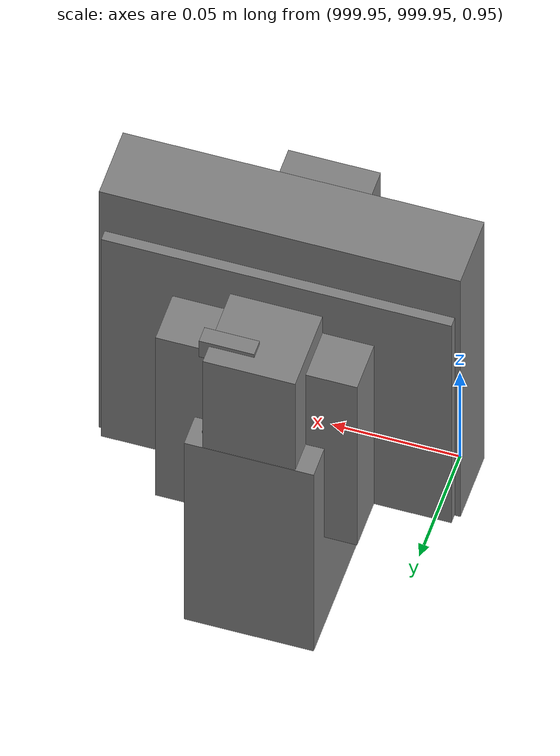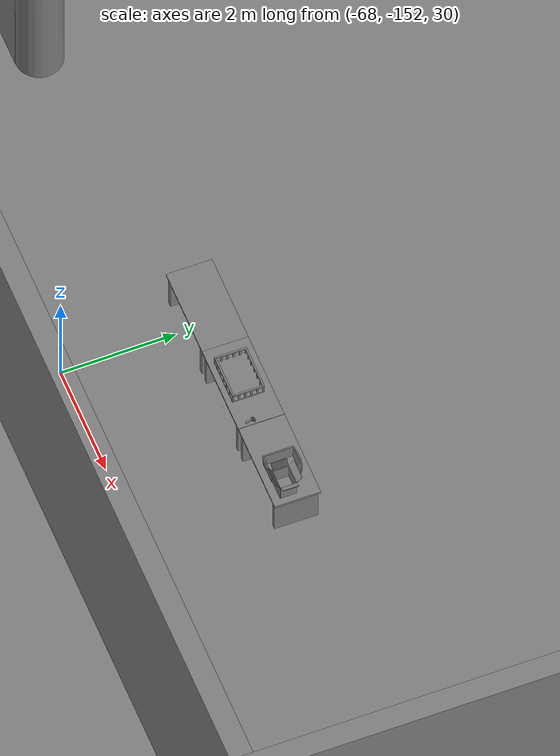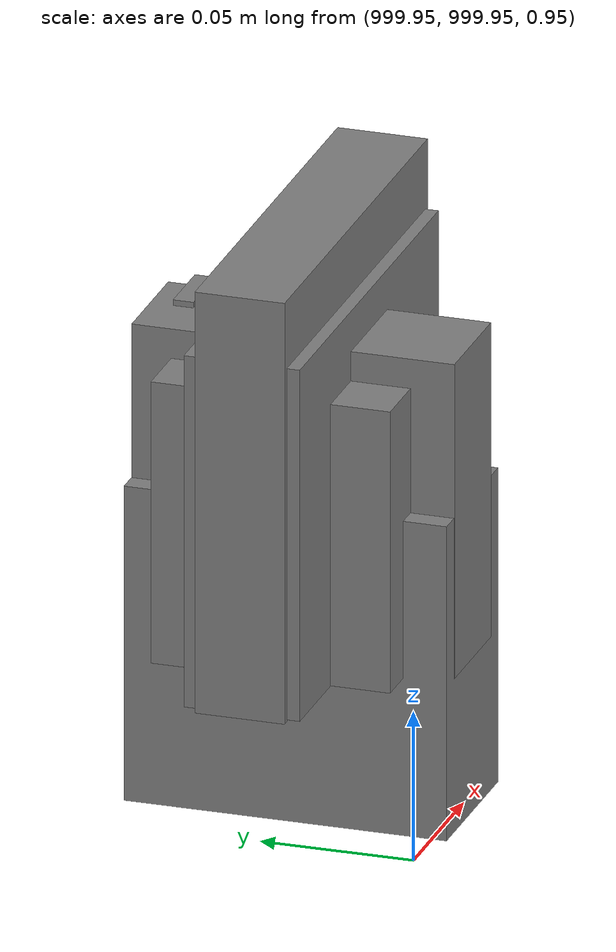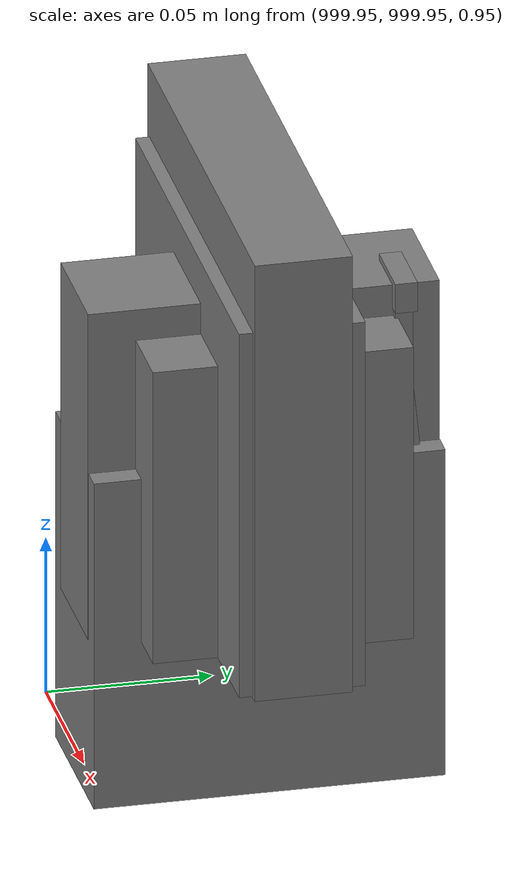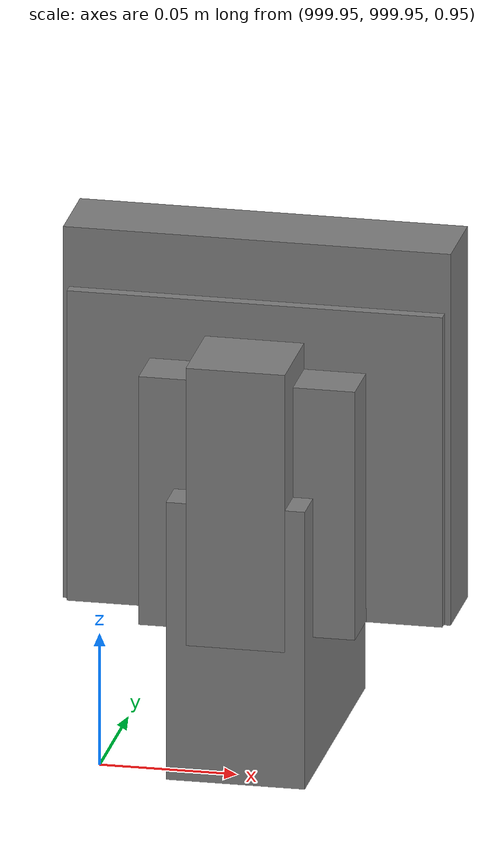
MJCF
<mujoco>
    <option gravity="0.000000000 0.000000000 -9.810000420" timestep="0.0049999999" integrator="implicitfast" density="1.225" viscosity="1.8000001e-05" noslip_iterations="10" iterations="100" sdf_iterations="50">
        <flag multiccd="disable"/>
    </option>
    <size memory="1000M"/>
    <compiler coordinate="local"/>
    <worldbody>
        <light cutoff="30" pos="0 1 1" dir="0 -1 -2"/>
        <light cutoff="30" pos="0 -1 1" dir="0 1 -2"/>
        <body pos="-65.915496826 -148.859542847 31.166849136" euler="9.786598206 -43.713748932 -122.893920898" mocap="true" name="spotlight4_SpotLight"/>
        <body pos="1000.000000000 1000.000000000 1.000000000" euler="0.000000000 0.000000000 180.000000000" name="openloong_gripper_2f85_fix_base_usda_battery_01">
            <geom contype="1" conaffinity="1" density="1000" type="box" material="" rgba="0.500000000 0.500000000 0.500000000 1.000000000" solimp="0.899999976 0.949999988 0.001000000" friction="1.000000000 0.005000000 0.000100000" solref="0.020000000 1.000000000" margin="0" condim="3" group="0" pos="-0.011123657 -0.041940309 0.101691343" quat="1.000000000 0.000000000 0.000000000 0.000000000" size="0.010800000 0.003375000 0.004725000" name="openloong_gripper_2f85_fix_base_usda_geom_51892433_221A_4FF9_9C2F_75B1C78A8198"/>
            <geom contype="1" conaffinity="1" density="1000" type="box" material="" rgba="0.500000000 0.500000000 0.500000000 1.000000000" solimp="0.899999976 0.949999988 0.001000000" friction="1.000000000 0.005000000 0.000100000" solref="0.020000000 1.000000000" margin="0" condim="3" group="0" pos="-0.010876465 -0.044247437 0.047066893" quat="0.998702705 -0.050920475 0.000000000 0.000000000" size="0.009450001 0.002700000 0.024975000" name="openloong_gripper_2f85_fix_base_usda_geom_15961832_55C0_4F0F_828F_CE906CBB5754"/>
            <geom contype="1" conaffinity="1" density="1000" type="box" material="" rgba="0.500000000 0.500000000 0.500000000 1.000000000" solimp="0.899999976 0.949999988 0.001000000" friction="1.000000000 0.005000000 0.000100000" solref="0.020000000 1.000000000" margin="0" condim="3" group="0" pos="-0.001235962 -0.000659180 0.047381196" quat="1.000000000 0.000000000 0.000000000 0.000000000" size="0.039420001 0.039150000 0.047250003" name="openloong_gripper_2f85_fix_base_usda_geom_7009BE7A_284C_4B20_82D8_926EDDF786B2"/>
            <geom contype="1" conaffinity="1" density="1000" type="box" material="" rgba="0.500000000 0.500000000 0.500000000 1.000000000" solimp="0.899999976 0.949999988 0.001000000" friction="1.000000000 0.005000000 0.000100000" solref="0.020000000 1.000000000" margin="0" condim="3" group="0" pos="-0.010876465 -0.039138794 0.009851727" quat="1.000000000 0.000000000 0.000000000 0.000000000" size="0.009450001 0.010800000 0.013500000" name="openloong_gripper_2f85_fix_base_usda_geom_C42957CF_ED99_476D_BF11_322F854AFB3C"/>
            <geom contype="1" conaffinity="1" density="1000" type="box" material="" rgba="0.500000000 0.500000000 0.500000000 1.000000000" solimp="0.899999976 0.949999988 0.001000000" friction="1.000000000 0.005000000 0.000100000" solref="0.020000000 1.000000000" margin="0" condim="3" group="0" pos="-0.010876465 -0.041528322 0.071508206" quat="1.000000000 0.000000000 0.000000000 0.000000000" size="0.009450001 0.002700000 0.027000001" name="openloong_gripper_2f85_fix_base_usda_geom_BD4011AD_2038_43B3_856D_31BB7D0C1ED4"/>
            <freejoint name="openloong_gripper_2f85_fix_base_usda_battery_01_joint"/>
            <site size="0.005000000 0.005000000 0.005000000" rgba="0.500000000 0.500000000 0.500000000 1.000000000" pos="0.000000000 0.000000000 0.000000000" quat="0.999961913 0.008726500 0.000000000 0.000000000" group="0" type="sphere" name="openloong_gripper_2f85_fix_base_usda_battery_01site"/>
        </body>
        <body pos="1000.000000000 1000.000000000 1.000000000" euler="0.000000000 0.000000000 180.000000000" name="openloong_gripper_2f85_fix_base_usda_cpu_fan">
            <geom contype="1" conaffinity="1" density="1000" type="box" material="" rgba="0.500000000 0.500000000 0.500000000 1.000000000" solimp="0.899999976 0.949999988 0.001000000" friction="1.000000000 0.005000000 0.000100000" solref="0.020000000 1.000000000" margin="0" condim="3" group="0" pos="0.000000000 0.000000000 0.070034981" quat="0.000000000 0.000000000 0.000000000 1.000000000" size="0.070700005 0.014699999 0.070700005" name="openloong_gripper_2f85_fix_base_usda_geom_0DC3FF14_EF3B_4F54_B098_2C55E762639E"/>
            <freejoint name="openloong_gripper_2f85_fix_base_usda_cpu_fan_joint"/>
            <site size="0.005000000 0.005000000 0.005000000" rgba="0.500000000 0.500000000 0.500000000 1.000000000" pos="0.000000000 0.000000000 0.000000000" quat="0.999961913 0.008726535 0.000000000 0.000000000" group="0" type="sphere" name="openloong_gripper_2f85_fix_base_usda_cpu_fancsite"/>
        </body>
        <body pos="1000.000000000 1000.000000000 1.000000000" euler="0.000000000 0.000000000 180.000000000" name="openloong_gripper_2f85_fix_base_usda_wifi_box">
            <geom contype="1" conaffinity="1" density="1000" type="box" material="" rgba="0.500000000 0.500000000 0.500000000 1.000000000" solimp="0.899999976 0.949999988 0.001000000" friction="1.000000000 0.005000000 0.000100000" solref="0.020000000 1.000000000" margin="0" condim="3" group="0" pos="0.000000000 0.000000000 0.058978677" quat="0.000000000 0.000000047 0.000000000 1.000000000" size="0.068499997 0.018999999 0.059000000" name="openloong_gripper_2f85_fix_base_usda_geom_109B2FB4_ECAA_468D_AA3C_4529EA5A7C47"/>
            <freejoint name="openloong_gripper_2f85_fix_base_usda_wifi_box_joint"/>
            <site size="0.005000000 0.005000000 0.005000000" rgba="0.500000000 0.500000000 0.500000000 1.000000000" pos="0.000000000 0.000000000 0.000000000" quat="0.999961913 0.008726500 0.000000000 0.000000000" group="0" type="sphere" name="openloong_gripper_2f85_fix_base_usda_wifi_boxsite"/>
        </body>
        <body pos="1000.000000000 1000.000000000 1.000000000" euler="0.000011953 0.000005123 -179.999984741" name="openloong_gripper_2f85_fix_base_usda_intel_box">
            <geom contype="1" conaffinity="1" density="1000" type="box" material="" rgba="0.500000000 0.500000000 0.500000000 1.000000000" solimp="0.899999976 0.949999988 0.001000000" friction="1.000000000 0.005000000 0.000100000" solref="0.020000000 1.000000000" margin="0" condim="3" group="0" pos="0.000000000 -0.000067139 0.000082284" quat="0.707106709 0.000000225 0.000000253 0.707106650" size="0.052800003 0.025300000 0.052800003" name="openloong_gripper_2f85_fix_base_usda_geom_CD96D577_F0CA_4289_B7B2_4C65A01BC334"/>
            <freejoint name="openloong_gripper_2f85_fix_base_usda_intel_box_joint"/>
            <site size="0.005000000 0.005000000 0.005000000" rgba="0.500000000 0.500000000 0.500000000 1.000000000" pos="0.000000000 0.000000000 0.000000000" quat="0.999961913 0.008726500 0.000000000 0.000000000" group="0" type="sphere" name="openloong_gripper_2f85_fix_base_usda_intel_boxsite"/>
        </body>
        <body pos="-66.126518250 -148.884857178 31.162750244" euler="-2.883242369 28.084703445 -118.021934509" mocap="true" name="spotlight5_SpotLight"/>
        <body pos="-66.275886536 -148.816711426 31.162162781" euler="-126.473060608 29.223651886 -82.934669495" mocap="true" name="spotlight2_SpotLight"/>
        <body pos="1000.000000000 999.999938965 1.000000000" euler="0.000000000 0.000000000 180.000000000" name="openloong_gripper_2f85_fix_base_usda_intelcore_i5">
            <geom contype="1" conaffinity="1" density="1000" type="box" material="" rgba="0.500000000 0.500000000 0.500000000 1.000000000" solimp="0.899999976 0.949999988 0.001000000" friction="1.000000000 0.005000000 0.000100000" solref="0.020000000 1.000000000" margin="0" condim="3" group="0" pos="0.000000000 0.000000000 0.051722717" quat="0.707106709 0.000000000 0.000000000 -0.707106769" size="0.052800000 0.018080002 0.052800000" name="openloong_gripper_2f85_fix_base_usda_geom_204BF2BF_9A58_4E6C_9349_3FE39E28B21C"/>
            <freejoint name="openloong_gripper_2f85_fix_base_usda_intelcore_i5_joint"/>
            <site size="0.005000000 0.005000000 0.005000000" rgba="0.500000000 0.500000000 0.500000000 1.000000000" pos="0.000000000 0.000000000 0.000000000" quat="0.999961913 0.008726534 0.000000000 0.000000000" group="0" type="sphere" name="openloong_gripper_2f85_fix_base_usda_intelcore_i5site"/>
        </body>
        <body pos="-64.866622925 -149.383972168 30.183746338" euler="89.999984741 89.999946594 0.000000000" name="openloong_gripper_2f85_fix_base_usda_bluebox_01">
            <geom contype="1" conaffinity="1" density="1000" type="box" material="" rgba="0.500000000 0.500000000 0.500000000 1.000000000" solimp="0.899999976 0.949999988 0.001000000" friction="1.000000000 0.005000000 0.000100000" solref="0.020000000 1.000000000" margin="0" condim="3" group="0" pos="0.276580811 0.187225342 0.000068665" quat="0.707106948 0.000077471 0.707106352 0.000077486" size="0.100000001 0.057999998 0.010000000" name="openloong_gripper_2f85_fix_base_usda_geom_7EB204BA_ABCF_47EF_BE5C_27A8BCDFB430"/>
            <geom contype="1" conaffinity="1" density="1000" type="box" material="" rgba="0.500000000 0.500000000 0.500000000 1.000000000" solimp="0.899999976 0.949999988 0.001000000" friction="1.000000000 0.005000000 0.000100000" solref="0.020000000 1.000000000" margin="0" condim="3" group="0" pos="0.000000000 0.002883911 0.000000000" quat="0.999999881 0.000000000 0.000000000 0.000000000" size="0.254000008 0.003000000 0.172000006" name="openloong_gripper_2f85_fix_base_usda_geom_D3D93ED3_9784_4506_8218_4FCB7F72B796"/>
            <geom contype="1" conaffinity="1" density="1000" type="box" material="" rgba="0.500000000 0.500000000 0.500000000 1.000000000" solimp="0.899999976 0.949999988 0.001000000" friction="1.000000000 0.005000000 0.000100000" solref="0.020000000 1.000000000" margin="0" condim="3" group="0" pos="0.000000000 0.124874115 0.173484802" quat="0.999796331 0.020176515 -0.000000015 0.000000030" size="0.259999990 0.119999997 0.007000000" name="openloong_gripper_2f85_fix_base_usda_geom_7CD4941E_0BE4_4792_B4D4_AE525031BB6C"/>
            <geom contype="1" conaffinity="1" density="1000" type="box" material="" rgba="0.500000000 0.500000000 0.500000000 1.000000000" solimp="0.899999976 0.949999988 0.001000000" friction="1.000000000 0.005000000 0.000100000" solref="0.020000000 1.000000000" margin="0" condim="3" group="0" pos="0.000000000 0.124874115 -0.173469543" quat="0.999796331 -0.020176545 -0.000000015 0.000000000" size="0.259999990 0.119999997 0.007000000" name="openloong_gripper_2f85_fix_base_usda_geom_B78514DE_6E14_4D3C_B965_A9BE55D80EC1"/>
            <geom contype="1" conaffinity="1" density="1000" type="box" material="" rgba="0.500000000 0.500000000 0.500000000 1.000000000" solimp="0.899999976 0.949999988 0.001000000" friction="1.000000000 0.005000000 0.000100000" solref="0.020000000 1.000000000" margin="0" condim="3" group="0" pos="0.000000000 0.214008331 0.188980103" quat="0.999912977 0.013176724 0.000000015 0.000000000" size="0.259999990 0.029999999 0.012500000" name="openloong_gripper_2f85_fix_base_usda_geom_0B1B7DB8_0E04_4935_B933_1E17D1AE8397"/>
            <geom contype="1" conaffinity="1" density="1000" type="box" material="" rgba="0.500000000 0.500000000 0.500000000 1.000000000" solimp="0.899999976 0.949999988 0.001000000" friction="1.000000000 0.005000000 0.000100000" solref="0.020000000 1.000000000" margin="0" condim="3" group="0" pos="-0.258361816 0.125289917 0.001876831" quat="0.702796936 -0.020792112 0.710783124 0.020769298" size="0.189999998 0.119999997 0.009000000" name="openloong_gripper_2f85_fix_base_usda_geom_F37723D5_D68B_4141_B197_A1CCD56ABC98"/>
            <geom contype="1" conaffinity="1" density="1000" type="box" material="" rgba="0.500000000 0.500000000 0.500000000 1.000000000" solimp="0.899999976 0.949999988 0.001000000" friction="1.000000000 0.005000000 0.000100000" solref="0.020000000 1.000000000" margin="0" condim="3" group="0" pos="0.000000000 0.214008331 -0.188980103" quat="0.999912977 -0.013176769 0.000000030 0.000000015" size="0.259999990 0.029999999 0.012500000" name="openloong_gripper_2f85_fix_base_usda_geom_E173B470_237F_473A_961B_07B2CDF6AD99"/>
            <geom contype="1" conaffinity="1" density="1000" type="box" material="" rgba="0.500000000 0.500000000 0.500000000 1.000000000" solimp="0.899999976 0.949999988 0.001000000" friction="1.000000000 0.005000000 0.000100000" solref="0.020000000 1.000000000" margin="0" condim="3" group="0" pos="-0.276611328 0.187225342 0.000068665" quat="0.707106650 0.000077441 0.707106709 0.000077456" size="0.100000001 0.057999998 0.010000000" name="openloong_gripper_2f85_fix_base_usda_geom_07E1A655_1E54_41A3_B6AA_5107D0996151"/>
            <geom contype="1" conaffinity="1" density="1000" type="box" material="" rgba="0.500000000 0.500000000 0.500000000 1.000000000" solimp="0.899999976 0.949999988 0.001000000" friction="1.000000000 0.005000000 0.000100000" solref="0.020000000 1.000000000" margin="0" condim="3" group="0" pos="0.258331299 0.125289917 0.001876831" quat="0.702851415 0.018856421 0.710823774 -0.019329369" size="0.189999998 0.119999997 0.009000000" name="openloong_gripper_2f85_fix_base_usda_geom_3D315F10_A837_4024_ACA3_05ADA9206EA7"/>
            <freejoint name="openloong_gripper_2f85_fix_base_usda_bluebox_01_joint"/>
            <site size="0.005000000 0.005000000 0.005000000" rgba="0.500000000 0.500000000 0.500000000 1.000000000" pos="0.000000000 0.000000000 0.000000000" quat="0.999961913 0.008726534 0.000000000 0.000000000" group="0" type="sphere" name="openloong_gripper_2f85_fix_base_usda_bluebox_01site"/>
        </body>
        <body pos="-64.496299744 -149.491867065 30.235729218" euler="0.000000000 0.000000000 89.999946594" name="openloong_gripper_2f85_fix_base_usda_cardboardbox_01">
            <geom contype="1" conaffinity="1" density="1000" type="box" material="" rgba="0.500000000 0.500000000 0.500000000 1.000000000" solimp="0.899999976 0.949999988 0.001000000" friction="1.000000000 0.005000000 0.000100000" solref="0.020000000 1.000000000" margin="0" condim="3" group="0" pos="-0.003166199 -0.004086494 0.005052090" quat="1.000000000 0.000000000 0.000000000 0.000000000" size="0.142499998 0.177500010 0.005000000" name="openloong_gripper_2f85_fix_base_usda_geom_DB0491F4_0BCF_4EAB_9C1A_747440AB8F41"/>
            <geom contype="1" conaffinity="1" density="1000" type="box" material="" rgba="0.500000000 0.500000000 0.500000000 1.000000000" solimp="0.899999976 0.949999988 0.001000000" friction="1.000000000 0.005000000 0.000100000" solref="0.020000000 1.000000000" margin="0" condim="3" group="0" pos="-0.003166199 0.170316696 0.150570869" quat="1.000000000 0.000000000 0.000000000 0.000000000" size="0.142499998 0.005000000 0.149999991" name="openloong_gripper_2f85_fix_base_usda_geom_2C3CBE8D_DDA1_483C_B85C_43B7F86E9BCF"/>
            <geom contype="1" conaffinity="1" density="1000" type="box" material="" rgba="0.500000000 0.500000000 0.500000000 1.000000000" solimp="0.899999976 0.949999988 0.001000000" friction="1.000000000 0.005000000 0.000100000" solref="0.020000000 1.000000000" margin="0" condim="3" group="0" pos="-0.147399902 -0.005307198 0.150570869" quat="1.000000000 0.000000000 0.000000000 0.000000000" size="0.005000000 0.177500010 0.149999991" name="openloong_gripper_2f85_fix_base_usda_geom_BAACEE91_82D4_421C_A938_01D0F07C0008"/>
            <geom contype="1" conaffinity="1" density="1000" type="box" material="" rgba="0.500000000 0.500000000 0.500000000 1.000000000" solimp="0.899999976 0.949999988 0.001000000" friction="1.000000000 0.005000000 0.000100000" solref="0.020000000 1.000000000" margin="0" condim="3" group="0" pos="0.140275955 -0.005307198 0.150570869" quat="1.000000000 0.000000000 0.000000000 0.000000000" size="0.005000000 0.177500010 0.149999991" name="openloong_gripper_2f85_fix_base_usda_geom_1C391C64_FE2E_4AC6_8C3A_255B45C5F60E"/>
            <geom contype="1" conaffinity="1" density="1000" type="box" material="" rgba="0.500000000 0.500000000 0.500000000 1.000000000" solimp="0.899999976 0.949999988 0.001000000" friction="1.000000000 0.005000000 0.000100000" solref="0.020000000 1.000000000" margin="0" condim="3" group="0" pos="-0.003166199 -0.181550980 0.150570869" quat="1.000000000 0.000000000 0.000000000 0.000000000" size="0.142499998 0.005000000 0.149999991" name="openloong_gripper_2f85_fix_base_usda_geom_614276FD_C68C_4364_8716_2DDB45011318"/>
            <freejoint name="openloong_gripper_2f85_fix_base_usda_cardboardbox_01_joint"/>
            <site size="0.005000000 0.005000000 0.005000000" rgba="0.500000000 0.500000000 0.500000000 1.000000000" pos="0.000000000 0.000000000 0.000000000" quat="0.999961913 0.008726535 0.000000000 0.000000000" group="0" type="sphere" name="openloong_gripper_2f85_fix_base_usda_site_06D78552_0320_4FF7_90B2_C64BAECCF5AD"/>
            <body pos="0.139160156 -0.004048347 0.301930904" euler="-179.999954224 49.383502960 179.999954224" name="openloong_gripper_2f85_fix_base_usda_A1_006">
                <geom contype="1" conaffinity="1" density="1000" type="box" material="" rgba="0.500000000 0.500000000 0.500000000 1.000000000" solimp="0.899999976 0.949999988 0.001000000" friction="1.000000000 0.005000000 0.000100000" solref="0.020000000 1.000000000" margin="0" condim="3" group="0" pos="-0.071587563 0.000009537 0.001745224" quat="0.999999881 0.000000000 0.000000000 0.000000000" size="0.071249999 0.179999992 0.002500000" name="openloong_gripper_2f85_fix_base_usda_geom_CD276DC0_ACA7_407B_AAAC_3955BFF91052"/>
                <joint armature="0" stiffness="0.07" damping="0.0099999998" axis="0.000000 1.000000 0.000000" type="hinge" name="openloong_gripper_2f85_fix_base_usda_A1_006"/>
            </body>
            <body pos="-0.145902634 -0.004086494 0.301938057" euler="-180.000000000 -60.000011444 -180.000000000" name="openloong_gripper_2f85_fix_base_usda_A2_006">
                <geom contype="1" conaffinity="1" density="1000" type="box" material="" rgba="0.500000000 0.500000000 0.500000000 1.000000000" solimp="0.899999976 0.949999988 0.001000000" friction="1.000000000 0.005000000 0.000100000" solref="0.020000000 1.000000000" margin="0" condim="3" group="0" pos="0.071268082 0.000009537 0.002717972" quat="0.000002921 0.000000000 -0.000000030 0.999999881" size="0.071249999 0.179999992 0.002500000" name="openloong_gripper_2f85_fix_base_usda_geom_4292E412_A5CB_462D_AF2C_9F3228282370"/>
                <joint armature="0" stiffness="0.07" damping="0.0099999998" axis="0.000000 1.000000 0.000000" type="hinge" name="openloong_gripper_2f85_fix_base_usda_A2_006"/>
            </body>
            <body pos="-0.003385544 0.175991058 0.301930904" euler="-125.858116150 -0.000004561 0.000002331" name="openloong_gripper_2f85_fix_base_usda_B2_006">
                <geom contype="1" conaffinity="1" density="1000" type="box" material="" rgba="0.500000000 0.500000000 0.500000000 1.000000000" solimp="0.899999976 0.949999988 0.001000000" friction="1.000000000 0.005000000 0.000100000" solref="0.020000000 1.000000000" margin="0" condim="3" group="0" pos="0.000009537 -0.070939064 -0.002470016" quat="0.999614120 0.027776197 -0.000000015 0.000000030" size="0.137500003 0.064999998 0.005000000" name="openloong_gripper_2f85_fix_base_usda_geom_7EDDFB50_0DDA_44AC_88F7_5EDFA5C819D1"/>
                <joint armature="0" stiffness="0.07" damping="0.0099999998" axis="1.000000 0.000000 0.000000" type="hinge" name="openloong_gripper_2f85_fix_base_usda_B2_006"/>
            </body>
            <body pos="-0.003385544 -0.184140205 0.301938057" euler="147.805557251 0.000000000 0.000000000" name="openloong_gripper_2f85_fix_base_usda_B1_006">
                <geom contype="1" conaffinity="1" density="1000" type="box" material="" rgba="0.500000000 0.500000000 0.500000000 1.000000000" solimp="0.899999976 0.949999988 0.001000000" friction="1.000000000 0.005000000 0.000100000" solref="0.020000000 1.000000000" margin="0" condim="3" group="0" pos="-0.000028610 0.070202351 -0.002703667" quat="0.999614179 -0.027776167 0.000000000 0.000000000" size="0.137500003 0.064999998 0.005000000" name="openloong_gripper_2f85_fix_base_usda_geom_AC5F4234_CC68_4638_B19D_49E0EBA05C69"/>
                <joint armature="0" stiffness="0.07" damping="0.0099999998" axis="1.000000 0.000000 0.000000" type="hinge" name="openloong_gripper_2f85_fix_base_usda_B1_006"/>
            </body>
        </body>
        <body pos="-65.882858276 -149.481979370 30.229999542" euler="-64.487716675 0.000000000 0.000000000" name="openloong_gripper_2f85_fix_base_usda_Barcode">
            <geom contype="1" conaffinity="1" density="1000" type="box" material="" rgba="0.500000000 0.500000000 0.500000000 1.000000000" solimp="0.899999976 0.949999988 0.001000000" friction="1.000000000 0.005000000 0.000100000" solref="0.020000000 1.000000000" margin="0" condim="3" group="0" pos="0.000000000 0.013038635 0.001419067" quat="0.000000000 0.000000000 0.000000000 1.000000119" size="0.034000002 0.010000000 0.017999999" name="openloong_gripper_2f85_fix_base_usda_geom_DAEA52A4_C776_42D9_9FC6_4575575D8A85"/>
            <geom contype="1" conaffinity="1" density="1000" type="box" material="" rgba="0.500000000 0.500000000 0.500000000 1.000000000" solimp="0.899999976 0.949999988 0.001000000" friction="1.000000000 0.005000000 0.000100000" solref="0.020000000 1.000000000" margin="0" condim="3" group="0" pos="0.000000000 -0.035301208 -0.007095337" quat="0.000000000 0.000000000 -0.043619365 0.999048233" size="0.028999999 0.010000000 0.020000000" name="openloong_gripper_2f85_fix_base_usda_geom_2BCA1423_A0E9_4C98_94E6_BB9393A6D61F"/>
            <geom contype="1" conaffinity="1" density="1000" type="box" material="" rgba="0.500000000 0.500000000 0.500000000 1.000000000" solimp="0.899999976 0.949999988 0.001000000" friction="1.000000000 0.005000000 0.000100000" solref="0.020000000 1.000000000" margin="0" condim="3" group="0" pos="0.000000000 -0.043411255 -0.011749268" quat="0.922262907 0.386563420 0.000000000 0.000000000" size="0.026000001 0.010000000 0.020000000" name="openloong_gripper_2f85_fix_base_usda_geom_5D50C43F_364A_427E_9BBB_1502822B64FF"/>
            <geom contype="1" conaffinity="1" density="1000" type="box" material="" rgba="0.500000000 0.500000000 0.500000000 1.000000000" solimp="0.899999976 0.949999988 0.001000000" friction="1.000000000 0.005000000 0.000100000" solref="0.020000000 1.000000000" margin="0" condim="3" group="0" pos="0.000000000 -0.016967773 -0.031860352" quat="0.000000000 0.000000000 0.000000000 1.000000119" size="0.008000000 0.010000000 0.013000000" name="openloong_gripper_2f85_fix_base_usda_geom_6CE7F0FE_CF24_4ECA_9988_8A0198412022"/>
            <geom contype="1" conaffinity="1" density="1000" type="box" material="" rgba="0.500000000 0.500000000 0.500000000 1.000000000" solimp="0.899999976 0.949999988 0.001000000" friction="1.000000000 0.005000000 0.000100000" solref="0.020000000 1.000000000" margin="0" condim="3" group="0" pos="0.000000000 -0.001869202 0.000312805" quat="0.953716993 0.300705761 0.000000000 0.000000000" size="0.032000002 0.010000000 0.018999999" name="openloong_gripper_2f85_fix_base_usda_geom_41560513_F3B5_45AD_878E_DA1309B8F743"/>
            <geom contype="1" conaffinity="1" density="1000" type="box" material="" rgba="0.500000000 0.500000000 0.500000000 1.000000000" solimp="0.899999976 0.949999988 0.001000000" friction="1.000000000 0.005000000 0.000100000" solref="0.020000000 1.000000000" margin="0" condim="3" group="0" pos="0.000000000 -0.019531250 -0.003173828" quat="0.953716993 0.300705761 0.000000000 0.000000000" size="0.030999999 0.010000000 0.020000000" name="openloong_gripper_2f85_fix_base_usda_geom_31FED648_551D_438E_8B09_B19D267B1174"/>
            <geom contype="1" conaffinity="1" density="1000" type="box" material="" rgba="0.500000000 0.500000000 0.500000000 1.000000000" solimp="0.899999976 0.949999988 0.001000000" friction="1.000000000 0.005000000 0.000100000" solref="0.020000000 1.000000000" margin="0" condim="3" group="0" pos="0.000000000 -0.035301208 -0.007095337" quat="0.953716993 0.300705761 0.000000000 0.000000000" size="0.028999999 0.010000000 0.020000000" name="openloong_gripper_2f85_fix_base_usda_geom_B26C16AD_F35C_49A2_A805_E2DAA692F584"/>
            <geom contype="1" conaffinity="1" density="1000" type="box" material="" rgba="0.500000000 0.500000000 0.500000000 1.000000000" solimp="0.899999976 0.949999988 0.001000000" friction="1.000000000 0.005000000 0.000100000" solref="0.020000000 1.000000000" margin="0" condim="3" group="0" pos="0.000000000 -0.042617798 -0.071121216" quat="0.000000000 0.000000000 0.000000000 1.000000119" size="0.013000000 0.021000000 0.059999999" name="openloong_gripper_2f85_fix_base_usda_geom_D6006695_FE75_4E9A_BE33_08239C2F5D51"/>
            <freejoint name="openloong_gripper_2f85_fix_base_usda_Barcode_joint"/>
            <site size="0.005000000 0.005000000 0.005000000" rgba="0.500000000 0.500000000 0.500000000 1.000000000" pos="0.000000000 0.000000000 0.000000000" quat="1.000000000 0.000000000 0.000000000 0.000000000" group="0" type="sphere" name="openloong_gripper_2f85_fix_base_usda_Barcode_site"/>
        </body>
        <body pos="-66.745018005 -149.392349243 30.184000015" euler="0.000000000 0.000000000 89.999946594" name="[22329793943578]_Basket_01">
            <geom contype="1" conaffinity="1" density="1000" type="box" material="" rgba="0.500000000 0.500000000 0.500000000 1.000000000" solimp="0.899999976 0.949999988 0.001000000" friction="1.000000000 0.005000000 0.000100000" solref="0.020000000 1.000000000" margin="0" condim="3" group="0" pos="-0.052425385 0.389207840 0.089787483" quat="0.707107008 0.000000000 0.000000000 0.707106411" size="0.014249999 0.014249999 0.059999999" name="[22329793943578]_geom_0C5530CF_F75E_4C66_A0E6_AECB682FA97D"/>
            <geom contype="1" conaffinity="1" density="1000" type="box" material="" rgba="0.500000000 0.500000000 0.500000000 1.000000000" solimp="0.899999976 0.949999988 0.001000000" friction="1.000000000 0.005000000 0.000100000" solref="0.020000000 1.000000000" margin="0" condim="3" group="0" pos="0.264015198 -0.133043289 0.089787483" quat="0.707107008 0.000000000 0.000000000 0.707106411" size="0.014249999 0.014249999 0.059999999" name="[22329793943578]_geom_A72524CD_C8B8_470D_AFE6_50F56DA98FAF"/>
            <geom contype="1" conaffinity="1" density="1000" type="box" material="" rgba="0.500000000 0.500000000 0.500000000 1.000000000" solimp="0.899999976 0.949999988 0.001000000" friction="1.000000000 0.005000000 0.000100000" solref="0.020000000 1.000000000" margin="0" condim="3" group="0" pos="-0.264015198 -0.265548706 0.089793205" quat="0.707107008 0.000000000 0.000000000 0.707106411" size="0.014249999 0.014249999 0.059999999" name="[22329793943578]_geom_86CF3718_7A59_4EED_93F4_2F3D8DF6CFDB"/>
            <geom contype="1" conaffinity="1" density="1000" type="box" material="" rgba="0.500000000 0.500000000 0.500000000 1.000000000" solimp="0.899999976 0.949999988 0.001000000" friction="1.000000000 0.005000000 0.000100000" solref="0.020000000 1.000000000" margin="0" condim="3" group="0" pos="-0.160263062 -0.389322281 0.089793205" quat="0.707107008 0.000000000 0.000000000 0.707106411" size="0.014249999 0.014249999 0.059999999" name="[22329793943578]_geom_9FEDF64F_297E_4972_AC9A_6E520B7D447D"/>
            <geom contype="1" conaffinity="1" density="1000" type="box" material="" rgba="0.500000000 0.500000000 0.500000000 1.000000000" solimp="0.899999976 0.949999988 0.001000000" friction="1.000000000 0.005000000 0.000100000" solref="0.020000000 1.000000000" margin="0" condim="3" group="0" pos="0.162265778 -0.389322281 0.089787483" quat="0.707107008 0.000000000 0.000000000 0.707106411" size="0.014249999 0.014249999 0.059999999" name="[22329793943578]_geom_BF8E7888_B9C2_4242_B3F4_5BF67E6B5236"/>
            <geom contype="1" conaffinity="1" density="1000" type="box" material="" rgba="0.500000000 0.500000000 0.500000000 1.000000000" solimp="0.899999976 0.949999988 0.001000000" friction="1.000000000 0.005000000 0.000100000" solref="0.020000000 1.000000000" margin="0" condim="3" group="0" pos="0.264015198 0.389207840 0.089787483" quat="0.707107008 0.000000000 0.000000000 0.707106411" size="0.014249999 0.014249999 0.059999999" name="[22329793943578]_geom_AA35170D_9585_48DE_B784_3A4573203B37"/>
            <geom contype="1" conaffinity="1" density="1000" type="box" material="" rgba="0.500000000 0.500000000 0.500000000 1.000000000" solimp="0.899999976 0.949999988 0.001000000" friction="1.000000000 0.005000000 0.000100000" solref="0.020000000 1.000000000" margin="0" condim="3" group="0" pos="-0.264015198 -0.133043289 0.089793205" quat="0.707107008 0.000000000 0.000000000 0.707106411" size="0.014249999 0.014249999 0.059999999" name="[22329793943578]_geom_77FC3C6E_B5AC_4308_B1FA_282D956FF894"/>
            <geom contype="1" conaffinity="1" density="1000" type="box" material="" rgba="0.500000000 0.500000000 0.500000000 1.000000000" solimp="0.899999976 0.949999988 0.001000000" friction="1.000000000 0.005000000 0.000100000" solref="0.020000000 1.000000000" margin="0" condim="3" group="0" pos="-0.264026642 0.269256592 0.089793205" quat="0.707107008 0.000000000 0.000000000 0.707106411" size="0.014249999 0.014249999 0.059999999" name="[22329793943578]_geom_9F97B28E_9631_4A66_B3C5_783F3D7D142F"/>
            <geom contype="1" conaffinity="1" density="1000" type="box" material="" rgba="0.500000000 0.500000000 0.500000000 1.000000000" solimp="0.899999976 0.949999988 0.001000000" friction="1.000000000 0.005000000 0.000100000" solref="0.020000000 1.000000000" margin="0" condim="3" group="0" pos="0.054462433 0.389207840 0.089787483" quat="0.707107008 0.000000000 0.000000000 0.707106411" size="0.014249999 0.014249999 0.059999999" name="[22329793943578]_geom_EB8AD210_640E_4168_9F42_0A218740B888"/>
            <geom contype="1" conaffinity="1" density="1000" type="box" material="" rgba="0.500000000 0.500000000 0.500000000 1.000000000" solimp="0.899999976 0.949999988 0.001000000" friction="1.000000000 0.005000000 0.000100000" solref="0.020000000 1.000000000" margin="0" condim="3" group="0" pos="0.054462433 -0.389322281 0.089787483" quat="0.707107008 0.000000000 0.000000000 0.707106411" size="0.014249999 0.014249999 0.059999999" name="[22329793943578]_geom_EA676EB8_D723_4484_9D6F_584FDF7A15FA"/>
            <geom contype="1" conaffinity="1" density="1000" type="box" material="" rgba="0.500000000 0.500000000 0.500000000 1.000000000" solimp="0.899999976 0.949999988 0.001000000" friction="1.000000000 0.005000000 0.000100000" solref="0.020000000 1.000000000" margin="0" condim="3" group="0" pos="0.264015198 0.269256592 0.089793205" quat="0.707107008 0.000000000 0.000000000 0.707106411" size="0.014249999 0.014249999 0.059999999" name="[22329793943578]_geom_A058AD7A_600A_4D18_AC01_AD3F241D1E45"/>
            <geom contype="1" conaffinity="1" density="1000" type="box" material="" rgba="0.500000000 0.500000000 0.500000000 1.000000000" solimp="0.899999976 0.949999988 0.001000000" friction="1.000000000 0.005000000 0.000100000" solref="0.020000000 1.000000000" margin="0" condim="3" group="0" pos="0.264015198 -0.389322281 0.089787483" quat="0.707107008 0.000000000 0.000000000 0.707106411" size="0.014249999 0.014249999 0.059999999" name="[22329793943578]_geom_4FBB2DBE_44C4_484C_9534_FD8FFD79683D"/>
            <geom contype="1" conaffinity="1" density="1000" type="box" material="" rgba="0.500000000 0.500000000 0.500000000 1.000000000" solimp="0.899999976 0.949999988 0.001000000" friction="1.000000000 0.005000000 0.000100000" solref="0.020000000 1.000000000" margin="0" condim="3" group="0" pos="0.000000000 0.000000000 0.015998840" quat="0.707107008 0.000000000 0.000000000 0.707106411" size="0.403499991 0.279000014 0.015750000" name="[22329793943578]_geom_824D3398_42B0_4D0B_B031_B7E0CF5F3981"/>
            <geom contype="1" conaffinity="1" density="1000" type="box" material="" rgba="0.500000000 0.500000000 0.500000000 1.000000000" solimp="0.899999976 0.949999988 0.001000000" friction="1.000000000 0.005000000 0.000100000" solref="0.020000000 1.000000000" margin="0" condim="3" group="0" pos="0.000000000 -0.389476776 0.163619041" quat="0.707107008 0.000000000 0.000000000 0.707106411" size="0.015000000 0.277500004 0.015750000" name="[22329793943578]_geom_72D4C2DE_7B9B_49A8_9853_EC5F7F127848"/>
            <geom contype="1" conaffinity="1" density="1000" type="box" material="" rgba="0.500000000 0.500000000 0.500000000 1.000000000" solimp="0.899999976 0.949999988 0.001000000" friction="1.000000000 0.005000000 0.000100000" solref="0.020000000 1.000000000" margin="0" condim="3" group="0" pos="0.162265778 0.389207840 0.089787483" quat="0.707107008 0.000000000 0.000000000 0.707106411" size="0.014249999 0.014249999 0.059999999" name="[22329793943578]_geom_39CBA4FA_3E55_498F_8CB0_43B1EF29B453"/>
            <geom contype="1" conaffinity="1" density="1000" type="box" material="" rgba="0.500000000 0.500000000 0.500000000 1.000000000" solimp="0.899999976 0.949999988 0.001000000" friction="1.000000000 0.005000000 0.000100000" solref="0.020000000 1.000000000" margin="0" condim="3" group="0" pos="0.000000000 0.389471054 0.163619041" quat="0.707107008 0.000000000 0.000000000 0.707106411" size="0.015000000 0.277500004 0.015750000" name="[22329793943578]_geom_67202BEE_F5B0_4205_AB34_B7116D4E5944"/>
            <geom contype="1" conaffinity="1" density="1000" type="box" material="" rgba="0.500000000 0.500000000 0.500000000 1.000000000" solimp="0.899999976 0.949999988 0.001000000" friction="1.000000000 0.005000000 0.000100000" solref="0.020000000 1.000000000" margin="0" condim="3" group="0" pos="-0.263511658 0.000000000 0.163619041" quat="0.707107008 0.000000000 0.000000000 0.707106411" size="0.403499991 0.015000000 0.015750000" name="[22329793943578]_geom_060492D4_87F8_4CBE_B8DC_3B5ABF203194"/>
            <geom contype="1" conaffinity="1" density="1000" type="box" material="" rgba="0.500000000 0.500000000 0.500000000 1.000000000" solimp="0.899999976 0.949999988 0.001000000" friction="1.000000000 0.005000000 0.000100000" solref="0.020000000 1.000000000" margin="0" condim="3" group="0" pos="-0.264015198 0.141334534 0.089793205" quat="0.707107008 0.000000000 0.000000000 0.707106411" size="0.014249999 0.014249999 0.059999999" name="[22329793943578]_geom_220D698E_5081_4AAB_9895_B43A2767F0F7"/>
            <geom contype="1" conaffinity="1" density="1000" type="box" material="" rgba="0.500000000 0.500000000 0.500000000 1.000000000" solimp="0.899999976 0.949999988 0.001000000" friction="1.000000000 0.005000000 0.000100000" solref="0.020000000 1.000000000" margin="0" condim="3" group="0" pos="0.264015198 -0.265548706 0.089787483" quat="0.707107008 0.000000000 0.000000000 0.707106411" size="0.014249999 0.014249999 0.059999999" name="[22329793943578]_geom_862BB44C_1F62_4CA3_9AD2_DAC12420F01E"/>
            <geom contype="1" conaffinity="1" density="1000" type="box" material="" rgba="0.500000000 0.500000000 0.500000000 1.000000000" solimp="0.899999976 0.949999988 0.001000000" friction="1.000000000 0.005000000 0.000100000" solref="0.020000000 1.000000000" margin="0" condim="3" group="0" pos="-0.160263062 0.389207840 0.089787483" quat="0.707107008 0.000000000 0.000000000 0.707106411" size="0.014249999 0.014249999 0.059999999" name="[22329793943578]_geom_A3200711_8287_4082_884E_9E8AFFD0E54F"/>
            <geom contype="1" conaffinity="1" density="1000" type="box" material="" rgba="0.500000000 0.500000000 0.500000000 1.000000000" solimp="0.899999976 0.949999988 0.001000000" friction="1.000000000 0.005000000 0.000100000" solref="0.020000000 1.000000000" margin="0" condim="3" group="0" pos="-0.052425385 -0.389322281 0.089787483" quat="0.707107008 0.000000000 0.000000000 0.707106411" size="0.014249999 0.014249999 0.059999999" name="[22329793943578]_geom_05BC61E5_A9BF_44EF_BDA8_70F4ADC187E6"/>
            <geom contype="1" conaffinity="1" density="1000" type="box" material="" rgba="0.500000000 0.500000000 0.500000000 1.000000000" solimp="0.899999976 0.949999988 0.001000000" friction="1.000000000 0.005000000 0.000100000" solref="0.020000000 1.000000000" margin="0" condim="3" group="0" pos="-0.264026642 -0.389322281 0.089793205" quat="0.707107008 0.000000000 0.000000000 0.707106411" size="0.014249999 0.014249999 0.059999999" name="[22329793943578]_geom_C2EA03F0_F620_4A09_BC43_9D0477E57F4D"/>
            <geom contype="1" conaffinity="1" density="1000" type="box" material="" rgba="0.500000000 0.500000000 0.500000000 1.000000000" solimp="0.899999976 0.949999988 0.001000000" friction="1.000000000 0.005000000 0.000100000" solref="0.020000000 1.000000000" margin="0" condim="3" group="0" pos="0.264015198 0.141334534 0.089787483" quat="0.707107008 0.000000000 0.000000000 0.707106411" size="0.014249999 0.014249999 0.059999999" name="[22329793943578]_geom_2EF3D6F6_CC65_41E5_9E24_C9FFAF720DB5"/>
            <geom contype="1" conaffinity="1" density="1000" type="box" material="" rgba="0.500000000 0.500000000 0.500000000 1.000000000" solimp="0.899999976 0.949999988 0.001000000" friction="1.000000000 0.005000000 0.000100000" solref="0.020000000 1.000000000" margin="0" condim="3" group="0" pos="-0.264015198 0.389207840 0.089793205" quat="0.707107008 0.000000000 0.000000000 0.707106411" size="0.014249999 0.014249999 0.059999999" name="[22329793943578]_geom_C33A94F9_9B64_4CC6_8EE1_37700FDE12F4"/>
            <geom contype="1" conaffinity="1" density="1000" type="box" material="" rgba="0.500000000 0.500000000 0.500000000 1.000000000" solimp="0.899999976 0.949999988 0.001000000" friction="1.000000000 0.005000000 0.000100000" solref="0.020000000 1.000000000" margin="0" condim="3" group="0" pos="0.264015198 0.004480362 0.089787483" quat="0.707107008 0.000000000 0.000000000 0.707106411" size="0.014249999 0.014249999 0.059999999" name="[22329793943578]_geom_8E72F86C_3BC1_42AE_8AEA_9BD183AB87CC"/>
            <geom contype="1" conaffinity="1" density="1000" type="box" material="" rgba="0.500000000 0.500000000 0.500000000 1.000000000" solimp="0.899999976 0.949999988 0.001000000" friction="1.000000000 0.005000000 0.000100000" solref="0.020000000 1.000000000" margin="0" condim="3" group="0" pos="0.263694763 -0.000011444 0.163619041" quat="0.707107008 0.000000000 0.000000000 0.707106411" size="0.403499991 0.015000000 0.015750000" name="[22329793943578]_geom_ACC15D4B_25E3_483B_9178_27AD447719E5"/>
            <geom contype="1" conaffinity="1" density="1000" type="box" material="" rgba="0.500000000 0.500000000 0.500000000 1.000000000" solimp="0.899999976 0.949999988 0.001000000" friction="1.000000000 0.005000000 0.000100000" solref="0.020000000 1.000000000" margin="0" condim="3" group="0" pos="-0.264015198 0.004480362 0.089793205" quat="0.707107008 0.000000000 0.000000000 0.707106411" size="0.014249999 0.014249999 0.059999999" name="[22329793943578]_geom_35E17399_D883_4E28_B4D0_7F82B630EE98"/>
            <freejoint name="[22329793943578]_joint_BBEFDFA3_5FD9_49B7_8296_2D5C18469739"/>
        </body>
        <body pos="0.000000000 0.000000000 0.000000000" euler="0.000000000 0.000000000 0.000000000" name="Static Objects_Static Objects">
            <geom contype="1" conaffinity="1" density="1000" type="box" material="" rgba="0.500000000 0.500000000 0.500000000 1.000000000" solimp="0.899999976 0.949999988 0.001000000" friction="1.000000000 0.005000000 0.000100000" solref="0.020000000 1.000000000" margin="0" condim="3" group="0" pos="-67.544113159 -149.365814209 29.727830887" quat="0.500000417 0.499999970 0.499999553 0.499999970" size="0.381000012 0.319999993 0.041000001" name="Static Objects_geom_44B2699B_6A74_440F_99BC_BBB4E7DFD49D"/>
            <geom contype="1" conaffinity="1" density="1000" type="box" material="" rgba="0.500000000 0.500000000 0.500000000 1.000000000" solimp="0.899999976 0.949999988 0.001000000" friction="1.000000000 0.005000000 0.000100000" solref="0.020000000 1.000000000" margin="0" condim="3" group="0" pos="-68.239501953 -149.365814209 30.086868286" quat="0.500000417 0.499999970 0.499999553 0.499999970" size="0.370999992 0.039500002 0.745000005" name="Static Objects_geom_751ABE71_E16E_41CE_99DD_A297ED020744"/>
            <geom contype="1" conaffinity="1" density="1000" type="box" material="" rgba="0.500000000 0.500000000 0.500000000 1.000000000" solimp="0.899999976 0.949999988 0.001000000" friction="1.000000000 0.005000000 0.000100000" solref="0.020000000 1.000000000" margin="0" condim="3" group="0" pos="-68.239501953 -149.365814209 30.147235870" quat="0.500000417 0.499999970 0.499999553 0.499999970" size="0.400000006 0.022000000 0.800000012" name="Static Objects_geom_2FF2B6C1_71ED_4C6B_8B12_0FC16E4DA581"/>
            <geom contype="1" conaffinity="1" density="1000" type="box" material="" rgba="0.500000000 0.500000000 0.500000000 1.000000000" solimp="0.899999976 0.949999988 0.001000000" friction="1.000000000 0.005000000 0.000100000" solref="0.020000000 1.000000000" margin="0" condim="3" group="0" pos="-68.934890747 -149.365814209 29.727830887" quat="0.500000417 0.499999970 0.499999553 0.499999970" size="0.381000012 0.319999993 0.041000001" name="Static Objects_geom_0988C048_E32D_4A47_B8CF_CB5F993E2BD7"/>
            <geom contype="1" conaffinity="1" density="1000" type="box" material="" rgba="0.500000000 0.500000000 0.500000000 1.000000000" solimp="0.899999976 0.949999988 0.001000000" friction="1.000000000 0.005000000 0.000100000" solref="0.020000000 1.000000000" margin="0" condim="3" group="0" pos="-68.239501953 -149.365814209 29.561563492" quat="0.500000417 0.499999970 0.499999553 0.499999970" size="0.020000000 0.022000000 0.660000026" name="Static Objects_geom_444F8D9F_3F59_4B05_99BE_05191E6F69A8"/>
            <geom contype="1" conaffinity="1" density="1000" type="box" material="" rgba="0.500000000 0.500000000 0.500000000 1.000000000" solimp="0.899999976 0.949999988 0.001000000" friction="1.000000000 0.005000000 0.000100000" solref="0.020000000 1.000000000" margin="0" condim="3" group="0" pos="-65.945671082 -149.365814209 29.727830887" quat="0.500000417 0.499999970 0.499999553 0.499999970" size="0.381000012 0.319999993 0.041000001" name="Static Objects_geom_8BED197C_28F1_4AAE_A382_F6C996D468C0"/>
            <geom contype="1" conaffinity="1" density="1000" type="box" material="" rgba="0.500000000 0.500000000 0.500000000 1.000000000" solimp="0.899999976 0.949999988 0.001000000" friction="1.000000000 0.005000000 0.000100000" solref="0.020000000 1.000000000" margin="0" condim="3" group="0" pos="-66.641059875 -149.365814209 30.086868286" quat="0.500000417 0.499999970 0.499999553 0.499999970" size="0.370999992 0.039500002 0.745000005" name="Static Objects_geom_63939B9C_4876_431B_AE2B_FFC894F845B3"/>
            <geom contype="1" conaffinity="1" density="1000" type="box" material="" rgba="0.500000000 0.500000000 0.500000000 1.000000000" solimp="0.899999976 0.949999988 0.001000000" friction="1.000000000 0.005000000 0.000100000" solref="0.020000000 1.000000000" margin="0" condim="3" group="0" pos="-66.641059875 -149.365814209 30.147235870" quat="0.500000417 0.499999970 0.499999553 0.499999970" size="0.400000006 0.022000000 0.800000012" name="Static Objects_geom_B15A68B4_8344_4DD8_AD7D_15E22AAC6B9B"/>
            <geom contype="1" conaffinity="1" density="1000" type="box" material="" rgba="0.500000000 0.500000000 0.500000000 1.000000000" solimp="0.899999976 0.949999988 0.001000000" friction="1.000000000 0.005000000 0.000100000" solref="0.020000000 1.000000000" margin="0" condim="3" group="0" pos="-67.336448669 -149.365814209 29.727830887" quat="0.500000417 0.499999970 0.499999553 0.499999970" size="0.381000012 0.319999993 0.041000001" name="Static Objects_geom_E83B222E_89C4_4593_B629_8505E4F87E2D"/>
            <geom contype="1" conaffinity="1" density="1000" type="box" material="" rgba="0.500000000 0.500000000 0.500000000 1.000000000" solimp="0.899999976 0.949999988 0.001000000" friction="1.000000000 0.005000000 0.000100000" solref="0.020000000 1.000000000" margin="0" condim="3" group="0" pos="-66.641059875 -149.365814209 29.561563492" quat="0.500000417 0.499999970 0.499999553 0.499999970" size="0.020000000 0.022000000 0.660000026" name="Static Objects_geom_2013DB21_D784_434A_904D_8E78294BDE22"/>
            <geom contype="1" conaffinity="1" density="1000" type="box" material="" rgba="0.500000000 0.500000000 0.500000000 1.000000000" solimp="0.899999976 0.949999988 0.001000000" friction="1.000000000 0.005000000 0.000100000" solref="0.020000000 1.000000000" margin="0" condim="3" group="0" pos="-64.338577271 -149.365814209 29.727830887" quat="0.500000417 0.499999970 0.499999553 0.499999970" size="0.381000012 0.319999993 0.041000001" name="Static Objects_geom_2502136C_9415_44AE_B061_795FC8E2B0D3"/>
            <geom contype="1" conaffinity="1" density="1000" type="box" material="" rgba="0.500000000 0.500000000 0.500000000 1.000000000" solimp="0.899999976 0.949999988 0.001000000" friction="1.000000000 0.005000000 0.000100000" solref="0.020000000 1.000000000" margin="0" condim="3" group="0" pos="-65.033966064 -149.365814209 30.086868286" quat="0.500000417 0.499999970 0.499999553 0.499999970" size="0.370999992 0.039500002 0.745000005" name="Static Objects_geom_975705B0_7359_4F9D_9E9A_B050B7C60BA8"/>
            <geom contype="1" conaffinity="1" density="1000" type="box" material="" rgba="0.500000000 0.500000000 0.500000000 1.000000000" solimp="0.899999976 0.949999988 0.001000000" friction="1.000000000 0.005000000 0.000100000" solref="0.020000000 1.000000000" margin="0" condim="3" group="0" pos="-65.033966064 -149.365814209 30.147235870" quat="0.500000417 0.499999970 0.499999553 0.499999970" size="0.400000006 0.022000000 0.800000012" name="Static Objects_geom_7F43C042_BE28_466E_A774_91F4D41FC011"/>
            <geom contype="1" conaffinity="1" density="1000" type="box" material="" rgba="0.500000000 0.500000000 0.500000000 1.000000000" solimp="0.899999976 0.949999988 0.001000000" friction="1.000000000 0.005000000 0.000100000" solref="0.020000000 1.000000000" margin="0" condim="3" group="0" pos="-65.729354858 -149.365814209 29.727830887" quat="0.500000417 0.499999970 0.499999553 0.499999970" size="0.381000012 0.319999993 0.041000001" name="Static Objects_geom_63B1EB8D_0498_4EF6_BFDE_C290750CF13D"/>
            <geom contype="1" conaffinity="1" density="1000" type="box" material="" rgba="0.500000000 0.500000000 0.500000000 1.000000000" solimp="0.899999976 0.949999988 0.001000000" friction="1.000000000 0.005000000 0.000100000" solref="0.020000000 1.000000000" margin="0" condim="3" group="0" pos="-65.033966064 -149.365814209 29.561563492" quat="0.500000417 0.499999970 0.499999553 0.499999970" size="0.020000000 0.022000000 0.660000026" name="Static Objects_geom_C1884E8B_1E16_4209_B721_6F334756C13F"/>
            <geom contype="1" conaffinity="1" density="1000" type="box" material="" rgba="0.500000000 0.500000000 0.500000000 1.000000000" solimp="0.899999976 0.949999988 0.001000000" friction="1.000000000 0.005000000 0.000100000" solref="0.020000000 1.000000000" margin="0" condim="3" group="0" pos="-61.754566193 -137.853729248 33.906845093" quat="0.707107067 0.000000000 0.000000000 0.707106471" size="0.759999990 0.759999990 4.500000000" name="Static Objects_geom_6DBB7C1E_6A5A_4D9F_A00D_93FE876D4229"/>
            <geom contype="1" conaffinity="1" density="1000" type="box" material="" rgba="0.500000000 0.500000000 0.500000000 1.000000000" solimp="0.899999976 0.949999988 0.001000000" friction="1.000000000 0.005000000 0.000100000" solref="0.020000000 1.000000000" margin="0" condim="3" group="0" pos="-57.511135101 -144.927108765 31.707921982" quat="1.000000000 0.000000000 0.000000000 0.000000000" size="0.200000003 8.000000000 2.299999952" name="Static Objects_geom_F35E75EE_0AFF_4272_B53F_46C7AF222AB9"/>
            <geom contype="1" conaffinity="1" density="1000" type="box" material="" rgba="0.500000000 0.500000000 0.500000000 1.000000000" solimp="0.899999976 0.949999988 0.001000000" friction="1.000000000 0.005000000 0.000100000" solref="0.020000000 1.000000000" margin="0" condim="3" group="0" pos="-80.517646790 -157.574050903 31.688196182" quat="0.707107067 0.000000000 0.000000000 0.707106471" size="0.600000024 0.600000024 2.299999952" name="Static Objects_geom_CD44DE01_0814_4CA0_817E_F9EC8594F6CC"/>
            <geom contype="1" conaffinity="1" density="1000" type="box" material="" rgba="0.500000000 0.500000000 0.500000000 1.000000000" solimp="0.899999976 0.949999988 0.001000000" friction="1.000000000 0.005000000 0.000100000" solref="0.020000000 1.000000000" margin="0" condim="3" group="0" pos="-80.711044312 -147.414932251 31.666158676" quat="1.000000000 0.000000000 0.000000000 0.000000000" size="0.200000003 10.000000000 2.299999952" name="Static Objects_geom_1727EBF2_9DED_43C9_B443_A85CDCFA746F"/>
            <geom contype="1" conaffinity="1" density="1000" type="box" material="" rgba="0.500000000 0.500000000 0.500000000 1.000000000" solimp="0.899999976 0.949999988 0.001000000" friction="1.000000000 0.005000000 0.000100000" solref="0.020000000 1.000000000" margin="0" condim="3" group="0" pos="-57.687217712 -137.434692383 31.688196182" quat="0.707107067 0.000000000 0.000000000 0.707106471" size="0.600000024 0.600000024 2.299999952" name="Static Objects_geom_982BE48D_660C_411A_A12B_7905AB70C693"/>
            <geom contype="1" conaffinity="1" density="1000" type="box" material="" rgba="0.500000000 0.500000000 0.500000000 1.000000000" solimp="0.899999976 0.949999988 0.001000000" friction="1.000000000 0.005000000 0.000100000" solref="0.020000000 1.000000000" margin="0" condim="3" group="0" pos="-69.537033081 -140.263229370 31.714921951" quat="0.707107067 0.000000000 0.000000000 0.707106471" size="0.759999990 4.500000000 2.299999952" name="Static Objects_geom_A92FD565_1B3B_4341_8D95_9BB26CBAF7D4"/>
            <geom contype="1" conaffinity="1" density="1000" type="box" material="" rgba="0.500000000 0.500000000 0.500000000 1.000000000" solimp="0.899999976 0.949999988 0.001000000" friction="1.000000000 0.005000000 0.000100000" solref="0.020000000 1.000000000" margin="0" condim="3" group="0" pos="-80.073638916 -137.853713989 33.906845093" quat="0.707107067 0.000000000 0.000000000 0.707106471" size="0.759999990 0.759999990 4.500000000" name="Static Objects_geom_C924003C_C05F_40C5_82FD_C9DB86367D25"/>
            <geom contype="1" conaffinity="1" density="1000" type="box" material="" rgba="0.500000000 0.500000000 0.500000000 1.000000000" solimp="0.899999976 0.949999988 0.001000000" friction="1.000000000 0.005000000 0.000100000" solref="0.020000000 1.000000000" margin="0" condim="3" group="0" pos="-73.406707764 -155.734664917 31.707921982" quat="1.000000000 0.000000000 0.000000000 0.000000000" size="0.200000003 3.000000000 2.299999952" name="Static Objects_geom_2C439990_CE54_440A_B415_8CCBFBEF7D96"/>
            <geom contype="1" conaffinity="1" density="1000" type="box" material="" rgba="0.500000000 0.500000000 0.500000000 1.000000000" solimp="0.899999976 0.949999988 0.001000000" friction="1.000000000 0.005000000 0.000100000" solref="0.020000000 1.000000000" margin="0" condim="3" group="0" pos="-68.497543335 -137.448257446 31.707921982" quat="0.707107067 0.000000000 0.000000000 0.707106471" size="0.200000003 14.000000000 2.299999952" name="Static Objects_geom_17499991_4C8E_491A_AC1C_235003B1EA77"/>
            <geom contype="1" conaffinity="1" density="1000" type="cylinder" material="" rgba="0.500000000 0.500000000 0.500000000 1.000000000" solimp="0.899999976 0.949999988 0.001000000" friction="1.000000000 0.005000000 0.000100000" solref="0.020000000 1.000000000" margin="0" condim="3" group="0" pos="-68.868522644 -142.134506226 31.711090088" quat="0.707107067 0.000000000 0.000000000 0.707106471" size="0.509999990 2.299999952 1.000000000" name="Static Objects_geom_CB0CEF6E_194D_484B_852D_260ED45848BD"/>
            <geom contype="1" conaffinity="1" density="1000" type="plane" material="" rgba="0.500000000 0.500000000 0.500000000 1.000000000" solimp="0.899999976 0.949999988 0.001000000" friction="1.000000000 0.005000000 0.000100000" solref="0.020000000 1.000000000" margin="0" condim="3" group="0" pos="-72.873703003 -147.131927490 29.409669876" quat="1.000000000 0.000000000 0.000000000 0.000000000" size="18.000000000 14.000000000 1.000000000" name="Static Objects_geom_BBE3F3C0_D2EF_476A_8712_2B9F165EF97C"/>
            <geom contype="1" conaffinity="1" density="1000" type="box" material="" rgba="0.500000000 0.500000000 0.500000000 1.000000000" solimp="0.899999976 0.949999988 0.001000000" friction="1.000000000 0.005000000 0.000100000" solref="0.020000000 1.000000000" margin="0" condim="3" group="0" pos="-79.943580627 -157.782272339 31.707921982" quat="0.707107067 0.000000000 0.000000000 0.707106471" size="0.200000003 7.000000000 2.299999952" name="Static Objects_geom_42F8B7FD_8321_4922_B95D_5A9C6E472A77"/>
            <geom contype="1" conaffinity="1" density="1000" type="box" material="" rgba="0.500000000 0.500000000 0.500000000 1.000000000" solimp="0.899999976 0.949999988 0.001000000" friction="1.000000000 0.005000000 0.000100000" solref="0.020000000 1.000000000" margin="0" condim="3" group="0" pos="-65.421028137 -152.903442383 31.707921982" quat="0.707107067 0.000000000 0.000000000 0.707106471" size="0.200000003 7.800000191 2.299999952" name="Static Objects_geom_16078A9C_D6BC_4726_8907_3BBDA74AE38B"/>
            <geom contype="1" conaffinity="1" density="1000" type="box" material="" rgba="0.500000000 0.500000000 0.500000000 1.000000000" solimp="0.899999976 0.949999988 0.001000000" friction="1.000000000 0.005000000 0.000100000" solref="0.020000000 1.000000000" margin="0" condim="3" group="0" pos="-74.776908875 -149.964416504 31.688196182" quat="1.000000000 0.000000000 0.000000000 0.000000000" size="0.600000024 0.409999996 2.299999952" name="Static Objects_geom_4A47FED3_2753_47CB_B64E_CFDAACFD2A0A"/>
            <geom contype="1" conaffinity="1" density="1000" type="cylinder" material="" rgba="0.500000000 0.500000000 0.500000000 1.000000000" solimp="0.899999976 0.949999988 0.001000000" friction="1.000000000 0.005000000 0.000100000" solref="0.020000000 1.000000000" margin="0" condim="3" group="0" pos="-60.161884308 -142.134506226 31.711090088" quat="0.707107067 0.000000000 0.000000000 0.707106471" size="0.509999990 2.299999952 1.000000000" name="Static Objects_geom_685484D2_9ED4_45A7_BCAF_FB5664CE9ED3"/>
            <geom contype="1" conaffinity="1" density="1000" type="cylinder" material="" rgba="0.500000000 0.500000000 0.500000000 1.000000000" solimp="0.899999976 0.949999988 0.001000000" friction="1.000000000 0.005000000 0.000100000" solref="0.020000000 1.000000000" margin="0" condim="3" group="0" pos="-75.382453918 -149.963455200 31.711090088" quat="0.707107067 0.000000000 0.000000000 0.707106471" size="0.409999996 2.299999952 1.000000000" name="Static Objects_geom_E95C7F7B_5713_45B9_A297_02A15B24C5DF"/>
            <geom contype="1" conaffinity="1" density="1000" type="cylinder" material="" rgba="0.500000000 0.500000000 0.500000000 1.000000000" solimp="0.899999976 0.949999988 0.001000000" friction="1.000000000 0.005000000 0.000100000" solref="0.020000000 1.000000000" margin="0" condim="3" group="0" pos="-74.154960632 -149.963455200 31.711090088" quat="0.707107067 0.000000000 0.000000000 0.707106471" size="0.409999996 2.299999952 1.000000000" name="Static Objects_geom_65B8C244_6354_4C9B_97B1_0DF774C71B4F"/>
            <geom contype="1" conaffinity="1" density="1000" type="cylinder" material="" rgba="0.500000000 0.500000000 0.500000000 1.000000000" solimp="0.899999976 0.949999988 0.001000000" friction="1.000000000 0.005000000 0.000100000" solref="0.020000000 1.000000000" margin="0" condim="3" group="0" pos="-77.566612244 -142.134506226 31.711090088" quat="0.707107067 0.000000000 0.000000000 0.707106471" size="0.509999990 2.299999952 1.000000000" name="Static Objects_geom_AFC7554A_6325_4AF3_A987_34AF43469F76"/>
        </body>
        <body pos="-66.291030884 -149.869689941 29.018842697" euler="0.000000000 0.000000000 89.999946594" mocap="true" name="openloong_gripper_2f85_fix_base_usda_leftHandMocap"/>
        <body pos="-66.291030884 -149.869689941 29.018842697" euler="0.000000000 0.000000000 89.999946594" mocap="true" name="openloong_gripper_2f85_fix_base_usda_rightHandMocap"/>
        <body pos="-66.291030884 -149.869689941 30.218843460" euler="0.000000000 0.000000000 89.999946594" name="openloong_gripper_2f85_fix_base_usda_base_link">
            <geom contype="1" conaffinity="1" density="1000" type="mesh" material="" rgba="0.783999979 0.783999979 0.783999979 1.000000000" solimp="0.899999976 0.949999988 0.001000000" friction="1.000000000 0.005000000 0.000100000" solref="0.020000000 1.000000000" margin="0" condim="3" group="3" mesh="base_link" pos="0.000000000 0.000000000 0.000000000" quat="1.000000000 0.000000000 0.000000000 0.000000000" size="1.000000000 1.000000000 1.000000000" name="openloong_gripper_2f85_fix_base_usda__geom_7_62C30315_00D3_431F_8539_C44F3106BEB9"/>
            <site size="0.005000000 0.005000000 0.005000000" rgba="0.500000000 0.500000000 0.500000000 1.000000000" pos="0.000000000 0.000000000 0.000000000" quat="1.000000000 0.000000000 0.000000000 0.000000000" group="0" type="sphere" name="openloong_gripper_2f85_fix_base_usda_imu"/>
            <inertial mass="22.447001" pos="-0.005664100 -0.001336700 0.238289997" diaginertia="0.374352545 0.277180195 0.220617250" quat="0.999247074 0.035235517 -0.015086859 0.006023135"/>
            <body pos="0.000000000 0.000000000 0.299997330" euler="0.000000000 0.000000000 0.000000000" name="openloong_gripper_2f85_fix_base_usda_dummy_body">
                <geom contype="1" conaffinity="1" density="1000" type="sphere" material="" rgba="0.783999979 0.783999979 0.783999979 1.000000000" solimp="0.899999976 0.949999988 0.001000000" friction="1.000000000 0.005000000 0.000100000" solref="0.020000000 1.000000000" margin="0" condim="3" group="3" pos="0.000000000 0.000000000 0.000000000" quat="1.000000000 0.000000000 0.000000000 0.000000000" size="0.010000000 0.000000000 0.000000000" name="openloong_gripper_2f85_fix_base_usda__geom_8_75898054_5161_48F3_80BD_070807926C8B"/>
                <joint armature="0.0099999998" stiffness="0" damping="0.1" axis="0.000000 0.000000 1.000000" type="hinge" name="openloong_gripper_2f85_fix_base_usda_dummy_joint"/>
                <site size="0.010000000 0.005000000 0.005000000" rgba="0.500000000 0.500000000 0.500000000 1.000000000" pos="0.000000000 0.000000000 0.000000000" quat="1.000000000 0.000000000 0.000000000 0.000000000" group="3" type="sphere" name="openloong_gripper_2f85_fix_base_usda_dummy_site"/>
            </body>
            <body pos="0.009002686 0.000000000 0.406400681" euler="0.000000000 0.000000000 0.000000000" name="openloong_gripper_2f85_fix_base_usda_Link_head_yaw">
                <geom contype="1" conaffinity="1" density="1000" type="mesh" material="" rgba="0.783999979 0.783999979 0.783999979 1.000000000" solimp="0.899999976 0.949999988 0.001000000" friction="1.000000000 0.005000000 0.000100000" solref="0.020000000 1.000000000" margin="0" condim="3" group="3" mesh="Link_head_yaw" pos="0.000000000 0.000000000 0.000000000" quat="1.000000000 0.000000000 0.000000000 0.000000000" size="1.000000000 1.000000000 1.000000000" name="openloong_gripper_2f85_fix_base_usda__geom_10_7851F9C9_BD3B_4981_BFC8_D708175D11E2"/>
                <inertial mass="0.84249002" pos="0.000000000 -0.002081400 0.044801001" diaginertia="0.000700588 0.000629000 0.000553812" quat="0.706933022 -0.015675601 0.015677100 0.706933022"/>
                <body pos="0.000000000 -0.034599304 0.048500061" euler="0.000000000 0.000000000 0.000000000" name="openloong_gripper_2f85_fix_base_usda_Link_head_pitch">
                    <geom contype="1" conaffinity="1" density="1000" type="mesh" material="" rgba="0.783999979 0.783999979 0.783999979 1.000000000" solimp="0.899999976 0.949999988 0.001000000" friction="1.000000000 0.005000000 0.000100000" solref="0.020000000 1.000000000" margin="0" condim="3" group="3" mesh="Link_head_pitch" pos="0.000000000 0.000000000 0.000000000" quat="1.000000000 0.000000000 0.000000000 0.000000000" size="1.000000000 1.000000000 1.000000000" name="openloong_gripper_2f85_fix_base_usda__geom_12_8F078E1C_B1AE_43C6_9B01_57B61212C9BB"/>
                    <inertial mass="1.3943" pos="0.020569000 0.033004001 0.125000000" diaginertia="0.006381400 0.006289940 0.004481460" quat="0.973390222 0.008406822 0.228157058 0.019624906"/>
                    <body pos="0.000000000 0.029998779 0.000000000" euler="0.000000000 0.000000000 0.000000000" name="openloong_gripper_2f85_fix_base_usda_neck_center_body">
                        <site size="0.010000000 0.005000000 0.005000000" rgba="0.500000000 0.500000000 0.500000000 1.000000000" pos="0.000000000 0.000000000 0.000000000" quat="1.000000000 0.000000000 0.000000000 0.000000000" group="3" type="sphere" name="openloong_gripper_2f85_fix_base_usda_neck_center_site"/>
                        <body pos="0.020004272 0.000000000 0.149999619" euler="-0.000002229 39.998176575 -90.000205994" name="openloong_gripper_2f85_fix_base_usda_camera_head">
                            <site size="0.010000000 0.005000000 0.005000000" rgba="0.500000000 0.500000000 0.500000000 1.000000000" pos="0.000000000 0.000000000 0.000000000" quat="1.000000000 0.000000000 0.000000000 0.000000000" group="3" type="sphere" name="openloong_gripper_2f85_fix_base_usda_camera_head_site"/>
                        </body>
                    </body>
                </body>
            </body>
            <body pos="0.003997803 -0.161598206 0.392200470" euler="0.000000000 0.000000000 0.000000000" name="openloong_gripper_2f85_fix_base_usda_Link_arm_r_01">
                <geom contype="1" conaffinity="1" density="1000" type="mesh" material="" rgba="0.783999979 0.783999979 0.783999979 1.000000000" solimp="0.899999976 0.949999988 0.001000000" friction="1.000000000 0.005000000 0.000100000" solref="0.020000000 1.000000000" margin="0" condim="3" group="3" mesh="Link_arm_r_01" pos="0.000000000 0.000000000 0.000000000" quat="1.000000000 0.000000000 0.000000000 0.000000000" size="1.000000000 1.000000000 1.000000000" name="openloong_gripper_2f85_fix_base_usda__geom_14_E4835B87_F0C2_4420_B31D_74C2071C67CE"/>
                <joint armature="0.0099999998" stiffness="0" damping="1" axis="0.000000 -1.000000 0.000000" limited="true" range="-170.000015259 170.000015259" type="hinge" name="openloong_gripper_2f85_fix_base_usda_J_arm_r_01"/>
                <inertial mass="0.75641" pos="0.004494600 -0.038293999 -0.000001874" diaginertia="0.000842990 0.000803050 0.000587120" quat="-0.000163502 0.707098067 0.000812463 0.707115054"/>
                <body pos="-0.041992188 -0.041000366 0.000000000" euler="0.000000000 0.000000000 0.000000000" name="openloong_gripper_2f85_fix_base_usda_Link_arm_r_02">
                    <geom contype="1" conaffinity="1" density="1000" type="mesh" material="" rgba="0.783999979 0.783999979 0.783999979 1.000000000" solimp="0.899999976 0.949999988 0.001000000" friction="1.000000000 0.005000000 0.000100000" solref="0.020000000 1.000000000" margin="0" condim="3" group="3" mesh="Link_arm_r_02" pos="0.000000000 0.000000000 0.000000000" quat="1.000000000 0.000000000 0.000000000 0.000000000" size="1.000000000 1.000000000 1.000000000" name="openloong_gripper_2f85_fix_base_usda__geom_16_A1680368_D6C6_48BC_99AE_2A5C4276EE5E"/>
                    <joint armature="0.0099999998" stiffness="0" damping="1" axis="-1.000000 0.000000 0.000000" limited="true" range="-105.000244141 105.000244141" type="hinge" name="openloong_gripper_2f85_fix_base_usda_J_arm_r_02"/>
                    <inertial mass="0.98500001" pos="0.041999999 -0.067430697 0.000000000" diaginertia="0.002262690 0.001730990 0.001154020" quat="0.500000000 0.500000000 -0.500000000 0.500000000"/>
                    <body pos="0.041992188 -0.122596741 0.000000000" euler="0.000000000 0.000000000 0.000000000" name="openloong_gripper_2f85_fix_base_usda_Link_arm_r_03">
                        <geom contype="1" conaffinity="1" density="1000" type="mesh" material="" rgba="0.783999979 0.783999979 0.783999979 1.000000000" solimp="0.899999976 0.949999988 0.001000000" friction="1.000000000 0.005000000 0.000100000" solref="0.020000000 1.000000000" margin="0" condim="3" group="3" mesh="Link_arm_r_03" pos="0.000000000 0.000000000 0.000000000" quat="1.000000000 0.000000000 0.000000000 0.000000000" size="1.000000000 1.000000000 1.000000000" name="openloong_gripper_2f85_fix_base_usda__geom_18_DF0F697C_C16C_4D6C_81B2_0D2445A588DF"/>
                        <joint armature="0.0099999998" stiffness="0" damping="1" axis="0.000000 -1.000000 0.000000" limited="true" range="-170.000015259 170.000015259" type="hinge" name="openloong_gripper_2f85_fix_base_usda_J_arm_r_03"/>
                        <inertial mass="0.95899999" pos="-0.001413580 -0.164663002 0.020757901" diaginertia="0.002101340 0.002064590 0.000754802" quat="0.560480952 0.454391927 -0.443732947 0.531497955"/>
                        <body pos="0.035293579 -0.177406311 0.023998260" euler="0.000000000 0.000000000 0.000000000" name="openloong_gripper_2f85_fix_base_usda_Link_arm_r_04">
                            <geom contype="1" conaffinity="1" density="1000" type="mesh" material="" rgba="0.783999979 0.783999979 0.783999979 1.000000000" solimp="0.899999976 0.949999988 0.001000000" friction="1.000000000 0.005000000 0.000100000" solref="0.020000000 1.000000000" margin="0" condim="3" group="3" mesh="Link_arm_r_04" pos="0.000000000 0.000000000 0.000000000" quat="1.000000000 0.000000000 0.000000000 0.000000000" size="1.000000000 1.000000000 1.000000000" name="openloong_gripper_2f85_fix_base_usda__geom_20_5B95D9B6_2A91_434E_8790_FA352CFBDC31"/>
                            <joint armature="0.0099999998" stiffness="0" damping="1" axis="-1.000000 0.000000 0.000000" limited="true" range="0.000000000 170.000015259" type="hinge" name="openloong_gripper_2f85_fix_base_usda_J_arm_r_04"/>
                            <inertial mass="0.60000002" pos="-0.038727000 -0.060766999 -0.021003000" diaginertia="0.001092610 0.000712422 0.000645102" quat="0.327701002 0.632602990 -0.467366993 0.523443997"/>
                            <body pos="-0.035293579 -0.103492737 -0.023998260" euler="0.000000000 0.000000000 0.000000000" name="openloong_gripper_2f85_fix_base_usda_Link_arm_r_05">
                                <geom contype="1" conaffinity="1" density="1000" type="mesh" material="" rgba="0.783999979 0.783999979 0.783999979 1.000000000" solimp="0.899999976 0.949999988 0.001000000" friction="1.000000000 0.005000000 0.000100000" solref="0.020000000 1.000000000" margin="0" condim="3" group="3" mesh="Link_arm_r_05" pos="0.000000000 0.000000000 0.000000000" quat="1.000000000 0.000000000 0.000000000 0.000000000" size="1.000000000 1.000000000 1.000000000" name="openloong_gripper_2f85_fix_base_usda__geom_22_43882E4B_911A_4634_A8C8_09D68958672C"/>
                                <joint armature="0.0099999998" stiffness="0" damping="1" axis="0.000000 -1.000000 0.000000" limited="true" range="-170.000015259 170.000015259" type="hinge" name="openloong_gripper_2f85_fix_base_usda_J_arm_r_05"/>
                                <inertial mass="0.68976003" pos="0.000032712 -0.068658002 -0.000111780" diaginertia="0.002522510 0.002411100 0.000448695" quat="0.707660973 0.706543028 -0.002603360 0.002470550"/>
                                <body pos="-0.026489258 -0.196502686 0.000000000" euler="0.000000000 0.000000000 0.000000000" name="openloong_gripper_2f85_fix_base_usda_Link_arm_r_06">
                                    <geom contype="1" conaffinity="1" density="1000" type="mesh" material="" rgba="0.783999979 0.783999979 0.783999979 1.000000000" solimp="0.899999976 0.949999988 0.001000000" friction="1.000000000 0.005000000 0.000100000" solref="0.020000000 1.000000000" margin="0" condim="3" group="3" mesh="Link_arm_r_06" pos="0.000000000 0.000000000 0.000000000" quat="1.000000000 0.000000000 0.000000000 0.000000000" size="1.000000000 1.000000000 1.000000000" name="openloong_gripper_2f85_fix_base_usda__geom_24_7C098F2D_B6B9_4D9F_BBAF_A40C575696C0"/>
                                    <joint armature="0.0099999998" stiffness="0" damping="1" axis="1.000000 0.000000 0.000000" limited="true" range="-105.000244141 105.000244141" type="hinge" name="openloong_gripper_2f85_fix_base_usda_J_arm_r_06"/>
                                    <inertial mass="0.28" pos="0.026078001 -0.000000896 0.001663700" diaginertia="0.000156930 0.000145601 0.000104979" quat="0.707080841 0.001851080 0.001883810 0.707127810"/>
                                    <body pos="0.026489258 0.000000000 0.031799316" euler="0.000000000 0.000000000 0.000000000" name="openloong_gripper_2f85_fix_base_usda_Link_arm_r_07">
                                        <geom contype="1" conaffinity="1" density="1000" type="mesh" material="" rgba="0.783999979 0.783999979 0.783999979 1.000000000" solimp="0.899999976 0.949999988 0.001000000" friction="1.000000000 0.005000000 0.000100000" solref="0.020000000 1.000000000" margin="0" condim="3" group="3" mesh="Link_arm_r_07" pos="0.000000000 0.000000000 0.000000000" quat="1.000000000 0.000000000 0.000000000 0.000000000" size="1.000000000 1.000000000 1.000000000" name="openloong_gripper_2f85_fix_base_usda__geom_26_9864D890_5982_412A_BD9A_3E56BFC4BEF9"/>
                                        <joint armature="0.0099999998" stiffness="0" damping="1" axis="0.000000 0.000000 1.000000" limited="true" range="-60.000133514 60.000133514" type="hinge" name="openloong_gripper_2f85_fix_base_usda_J_arm_r_07"/>
                                        <inertial mass="0.61353999" pos="-0.007859000 -0.158170000 -0.027736001" diaginertia="0.003037610 0.002570910 0.000729379" quat="0.427542925 0.443532884 -0.553093910 0.560867906"/>
                                        <body pos="0.000000000 0.286994934 -0.270000458" euler="150.000350952 -0.000001649 -0.000000442" name="openloong_gripper_2f85_fix_base_usda_camera_wrist_r">
                                            <site size="0.010000000 0.005000000 0.005000000" rgba="0.500000000 0.500000000 0.500000000 1.000000000" pos="0.000000000 0.000000000 0.000000000" quat="1.000000000 0.000000000 0.000000000 0.000000000" group="3" type="sphere" name="openloong_gripper_2f85_fix_base_usda_camera_wrist_r_site"/>
                                        </body>
                                        <body pos="0.000000000 -0.220008850 -0.033002853" euler="0.000000000 0.000000000 179.999969482" name="openloong_gripper_2f85_fix_base_usda_ee_center_body_r">
                                            <site size="0.010000000 0.005000000 0.005000000" rgba="0.500000000 0.500000000 0.500000000 1.000000000" pos="0.000000000 0.000000000 0.000000000" quat="1.000000000 0.000000000 0.000000000 0.000000000" group="3" type="sphere" name="openloong_gripper_2f85_fix_base_usda_ee_center_site_r"/>
                                        </body>
                                        <body pos="0.000000000 -0.066001892 -0.031000137" euler="89.999984741 0.000000000 180.000000000" name="openloong_gripper_2f85_fix_base_usda_zbr_base_link">
                                            <geom contype="1" conaffinity="1" density="1000" type="mesh" material="" rgba="0.783999979 0.783999979 0.783999979 1.000000000" solimp="0.899999976 0.949999988 0.001000000" friction="1.000000000 0.005000000 0.000100000" solref="0.020000000 1.000000000" margin="0" condim="3" group="3" mesh="base" pos="0.000000000 0.000003815 -0.000007629" quat="1.000000000 0.000000000 0.000000000 0.000000000" size="1.000000238 1.000000238 1.000000238" name="openloong_gripper_2f85_fix_base_usda__geom_30_81685BAC_0F1E_4176_AE5B_4756641053C9"/>
                                            <inertial mass="0.77744102" pos="0.000000000 -0.000027039 0.035467502" diaginertia="0.000260285 0.000225381 0.000152708" quat="0.999998808 -0.001528488 0.000000000 0.000000000"/>
                                            <body pos="-0.030609138 0.004745484 0.065696731" euler="-89.999984741 -0.000000000 0.000000000" name="openloong_gripper_2f85_fix_base_usda_r_left_driver">
                                                <geom contype="1" conaffinity="1" density="1000" type="mesh" material="" rgba="0.783999979 0.783999979 0.783999979 1.000000000" solimp="0.899999976 0.949999988 0.001000000" friction="1.000000000 0.005000000 0.000100000" solref="0.020000000 1.000000000" margin="0" condim="3" group="3" mesh="driver" pos="0.030609138 0.054901138 -0.004699708" quat="0.707106829 0.707106709 0.000000000 -0.000000000" size="1.000000238 1.000000238 1.000000238" name="openloong_gripper_2f85_fix_base_usda__geom_32_E5CB2CCA_8F1C_4BEA_A639_134E90414982"/>
                                                <joint armature="0.0049999999" stiffness="0" damping="0.1" axis="0.000000 0.000000 1.000000" limited="true" range="0.000000000 51.566200256" type="hinge" name="openloong_gripper_2f85_fix_base_usda_r_left_driver_joint"/>
                                                <inertial mass="0.0089956298" pos="0.000000000 0.017754700 0.001073140" diaginertia="0.000001724 0.000001609 0.000000322" quat="0.681301236 0.732003212 0.000000000 0.000000000"/>
                                                <body pos="-0.031402595 0.004524232 -0.010200503" euler="0.000000000 0.000000000 180.000000000" name="openloong_gripper_2f85_fix_base_usda_r_left_coupler">
                                                    <geom contype="1" conaffinity="1" density="1000" type="mesh" material="" rgba="0.783999979 0.783999979 0.783999979 1.000000000" solimp="0.899999976 0.949999988 0.001000000" friction="1.000000000 0.005000000 0.000100000" solref="0.020000000 1.000000000" margin="0" condim="3" group="3" mesh="coupler" pos="-0.062011734 -0.050354015 0.005500795" quat="0.707106829 -0.707106709 0.000000000 -0.000000000" size="1.000000238 1.000000238 1.000000238" name="openloong_gripper_2f85_fix_base_usda__geom_34_AD181A79_45FD_4C48_88D0_471E414C11EF"/>
                                                    <inertial mass="0.0140974" pos="0.000000000 0.003012090 0.023217499" diaginertia="0.000004162 0.000003522 0.000000888" quat="0.705635548 -0.045590367 0.045590367 0.705635548"/>
                                                </body>
                                            </body>
                                            <body pos="-0.012695315 -0.012001040 0.072212234" euler="-89.999984741 -0.000000000 0.000000000" name="openloong_gripper_2f85_fix_base_usda_r_left_spring_link">
                                                <geom contype="1" conaffinity="1" density="1000" type="mesh" material="" rgba="0.783999979 0.783999979 0.783999979 1.000000000" solimp="0.899999976 0.949999988 0.001000000" friction="1.000000000 0.005000000 0.000100000" solref="0.020000000 1.000000000" margin="0" condim="3" group="3" mesh="spring_link" pos="0.012695315 0.061416641 0.012050631" quat="0.707106829 0.707106709 0.000000000 -0.000000000" size="1.000000238 1.000000238 1.000000238" name="openloong_gripper_2f85_fix_base_usda__geom_36_77584AF5_1E9C_4690_83DF_341B3600A78C"/>
                                                <joint armature="0.001" stiffness="0.050000001" damping="0.00125" axis="0.000000 0.000000 1.000000" limited="true" range="-17.000000000 51.566200256" type="hinge" name="openloong_gripper_2f85_fix_base_usda_r_left_spring_link_joint"/>
                                                <inertial mass="0.0221642" pos="-0.000000009 0.018162400 0.021265799" diaginertia="0.000008969 0.000006717 0.000002639" quat="0.663403213 -0.244737089 0.244737089 0.663403213"/>
                                                <body pos="-0.038208015 -0.042503368 0.002950669" euler="180.000000000 0.000000000 -0.002185660" name="openloong_gripper_2f85_fix_base_usda_r_left_follower">
                                                    <geom contype="1" conaffinity="1" density="1000" type="mesh" material="" rgba="0.783999979 0.783999979 0.783999979 1.000000000" solimp="0.899999976 0.949999988 0.001000000" friction="1.000000000 0.005000000 0.000100000" solref="0.020000000 1.000000000" margin="0" condim="3" group="3" mesh="tongue" pos="0.050918590 -0.103920005 -0.009099962" quat="0.707106829 -0.707106709 0.000000030 0.000000030" size="1.000000238 1.000000238 1.000000238" name="openloong_gripper_2f85_fix_base_usda__geom_40_9191A792_8195_4854_B301_857155EF2CF9"/>
                                                    <geom contype="1" conaffinity="1" density="1000" type="mesh" material="" rgba="0.783999979 0.783999979 0.783999979 1.000000000" solimp="0.899999976 0.949999988 0.001000000" friction="1.000000000 0.005000000 0.000100000" solref="0.020000000 1.000000000" margin="0" condim="3" group="3" mesh="follower" pos="0.050918590 -0.103920005 -0.009099962" quat="0.707106829 -0.707106709 0.000000030 0.000000030" size="1.000000238 1.000000238 1.000000238" name="openloong_gripper_2f85_fix_base_usda__geom_39_C3684CCA_5CF3_4BBE_85FE_D099F835A6D4"/>
                                                    <joint armature="0.001" stiffness="0" damping="0.1" axis="0.000000 0.000000 1.000000" limited="true" range="-49.999961853 51.566200256" type="hinge" name="openloong_gripper_2f85_fix_base_usda_r_left_follower"/>
                                                    <inertial mass="0.0125222" pos="0.000000000 -0.011046000 0.012478600" diaginertia="0.000002674 0.000002456 0.000000602" quat="0.986436546 0.164143041 0.000000000 0.000000000"/>
                                                    <body pos="-0.037765510 -0.103912376 -0.009099962" euler="-89.999984741 0.000000000 0.000004829" name="openloong_gripper_2f85_fix_base_usda_r_left_pad">
                                                        <geom contype="1" conaffinity="1" density="1000" type="box" material="" rgba="0.550000012 0.550000012 0.550000012 1.000000000" solimp="0.949999988 0.990000010 0.001000000" friction="0.699999988 0.005000000 0.000100000" solref="0.020000000 1.000000000" margin="0" condim="3" group="3" mass="1e-06" pos="0.043243419 0.000003815 0.119995147" quat="0.999999881 0.000000000 0.000000000 0.000000000" size="0.002000001 0.011000003 0.009375002" name="openloong_gripper_2f85_fix_base_usda_r_left_pad1_78E732A2_3E5C_4CE8_8685_6451BC0E2C4F"/>
                                                        <geom contype="1" conaffinity="1" density="1000" type="box" material="" rgba="0.449999988 0.449999988 0.449999988 1.000000000" solimp="0.949999988 0.990000010 0.001000000" friction="0.600000024 0.005000000 0.000100000" solref="0.020000000 1.000000000" margin="0" condim="3" group="3" mass="1e-06" pos="0.043243419 0.000003815 0.138748199" quat="0.999999881 0.000000000 0.000000000 0.000000000" size="0.002000001 0.011000003 0.009375002" name="openloong_gripper_2f85_fix_base_usda_r_left_pad2_E36E9244_198D_4E74_9F6F_039E09037C1E"/>
                                                    </body>
                                                </body>
                                            </body>
                                            <body pos="0.030593880 -0.004753114 0.065696731" euler="89.999984741 0.000000000 180.000000000" name="openloong_gripper_2f85_fix_base_usda_r_right_driver">
                                                <geom contype="1" conaffinity="1" density="1000" type="mesh" material="" rgba="0.783999979 0.783999979 0.783999979 1.000000000" solimp="0.899999976 0.949999988 0.001000000" friction="1.000000000 0.005000000 0.000100000" solref="0.020000000 1.000000000" margin="0" condim="3" group="3" mesh="driver" pos="0.030593880 0.054901138 -0.004699708" quat="0.707106829 0.707106709 0.000000000 0.000000000" size="1.000000238 1.000000238 1.000000238" name="openloong_gripper_2f85_fix_base_usda__geom_42_C8D84741_E738_4F30_A4E3_A2A7AFBEBF1A"/>
                                                <joint armature="0.0049999999" stiffness="0" damping="0.1" axis="0.000000 0.000000 1.000000" limited="true" range="0.000000000 51.566200256" type="hinge" name="openloong_gripper_2f85_fix_base_usda_r_right_driver_joint"/>
                                                <inertial mass="0.0089956298" pos="0.000000000 0.017754700 0.001073140" diaginertia="0.000001724 0.000001609 0.000000322" quat="0.681301236 0.732003212 0.000000000 0.000000000"/>
                                                <body pos="-0.031417854 0.004531861 -0.010202411" euler="0.000000000 0.000000000 180.000000000" name="openloong_gripper_2f85_fix_base_usda_r_right_coupler">
                                                    <geom contype="1" conaffinity="1" density="1000" type="mesh" material="" rgba="0.783999979 0.783999979 0.783999979 1.000000000" solimp="0.899999976 0.949999988 0.001000000" friction="1.000000000 0.005000000 0.000100000" solref="0.020000000 1.000000000" margin="0" condim="3" group="3" mesh="coupler" pos="-0.062042251 -0.050376903 0.005500795" quat="0.707106829 -0.707106709 0.000000000 0.000000000" size="1.000000238 1.000000238 1.000000238" name="openloong_gripper_2f85_fix_base_usda__geom_44_DD0BEF56_59A8_4D0A_B9BC_23211AB3255D"/>
                                                    <inertial mass="0.0140974" pos="0.000000000 0.003012090 0.023217499" diaginertia="0.000004162 0.000003522 0.000000888" quat="0.705635548 -0.045590367 0.045590367 0.705635548"/>
                                                </body>
                                            </body>
                                            <body pos="0.012695315 0.011997226 0.072219864" euler="89.999984741 0.000000000 180.000000000" name="openloong_gripper_2f85_fix_base_usda_r_right_spring_link">
                                                <geom contype="1" conaffinity="1" density="1000" type="mesh" material="" rgba="0.783999979 0.783999979 0.783999979 1.000000000" solimp="0.899999976 0.949999988 0.001000000" friction="1.000000000 0.005000000 0.000100000" solref="0.020000000 1.000000000" margin="0" condim="3" group="3" mesh="spring_link" pos="0.012695315 0.061424270 0.012048724" quat="0.707106829 0.707106709 0.000000000 0.000000000" size="1.000000238 1.000000238 1.000000238" name="openloong_gripper_2f85_fix_base_usda__geom_46_0D6F78EE_57BA_44AD_954A_0B793711DE7E"/>
                                                <joint armature="0.001" stiffness="0.050000001" damping="0.00125" axis="0.000000 0.000000 1.000000" limited="true" range="-17.000000000 51.566200256" type="hinge" name="openloong_gripper_2f85_fix_base_usda_r_right_spring_link_joint"/>
                                                <inertial mass="0.0221642" pos="-0.000000009 0.018162400 0.021265799" diaginertia="0.000008969 0.000006717 0.000002639" quat="0.663403213 -0.244737089 0.244737089 0.663403213"/>
                                                <body pos="-0.038208015 -0.042495739 0.002950669" euler="180.000000000 0.000000000 0.000000000" name="openloong_gripper_2f85_fix_base_usda_r_right_follower">
                                                    <geom contype="1" conaffinity="1" density="1000" type="mesh" material="" rgba="0.783999979 0.783999979 0.783999979 1.000000000" solimp="0.899999976 0.949999988 0.001000000" friction="1.000000000 0.005000000 0.000100000" solref="0.020000000 1.000000000" margin="0" condim="3" group="3" mesh="follower" pos="0.050888073 -0.103927635 -0.009099962" quat="0.707106829 -0.707106709 0.000000000 0.000000000" size="1.000000238 1.000000238 1.000000238" name="openloong_gripper_2f85_fix_base_usda__geom_50_C337CB7E_3EEE_4A8A_8A19_C043D715CFE1"/>
                                                    <geom contype="1" conaffinity="1" density="1000" type="mesh" material="" rgba="0.783999979 0.783999979 0.783999979 1.000000000" solimp="0.899999976 0.949999988 0.001000000" friction="1.000000000 0.005000000 0.000100000" solref="0.020000000 1.000000000" margin="0" condim="3" group="3" mesh="tongue" pos="0.050888073 -0.103927635 -0.009099962" quat="0.707106829 -0.707106709 0.000000000 0.000000000" size="1.000000238 1.000000238 1.000000238" name="openloong_gripper_2f85_fix_base_usda__geom_49_04281860_4263_46B8_BB15_2500FF980C98"/>
                                                    <joint armature="0.001" stiffness="0" damping="0.1" axis="0.000000 0.000000 1.000000" limited="true" range="-49.999961853 51.566200256" type="hinge" name="openloong_gripper_2f85_fix_base_usda_r_right_follower_joint"/>
                                                    <inertial mass="0.0125222" pos="0.000000000 -0.011046000 0.012478600" diaginertia="0.000002674 0.000002456 0.000000602" quat="0.986436546 0.164143041 0.000000000 0.000000000"/>
                                                    <body pos="-0.037811287 -0.103927635 -0.009099962" euler="-89.999984741 0.000000000 0.000000000" name="openloong_gripper_2f85_fix_base_usda_r_right_pad">
                                                        <geom contype="1" conaffinity="1" density="1000" type="box" material="" rgba="0.449999988 0.449999988 0.449999988 1.000000000" solimp="0.949999988 0.990000010 0.001000000" friction="0.600000024 0.005000000 0.000100000" solref="0.020000000 1.000000000" margin="0" condim="3" group="3" mass="1e-06" pos="0.043258678 0.000000000 0.138748199" quat="1.000000000 0.000000000 0.000000000 0.000000000" size="0.002000001 0.011000003 0.009375002" name="openloong_gripper_2f85_fix_base_usda_r_right_pad2_6C245770_9225_40A2_896A_34F87CCB98CB"/>
                                                        <geom contype="1" conaffinity="1" density="1000" type="box" material="" rgba="0.550000012 0.550000012 0.550000012 1.000000000" solimp="0.949999988 0.990000010 0.001000000" friction="0.699999988 0.005000000 0.000100000" solref="0.020000000 1.000000000" margin="0" condim="3" group="3" mass="1e-06" pos="0.043258678 0.000003815 0.120002776" quat="1.000000000 0.000000000 0.000000000 0.000000000" size="0.002000001 0.011000003 0.009375002" name="openloong_gripper_2f85_fix_base_usda_r_right_pad1_F9FDEB11_A981_4263_8E8D_BB134C8BC356"/>
                                                    </body>
                                                </body>
                                            </body>
                                        </body>
                                    </body>
                                </body>
                            </body>
                        </body>
                    </body>
                </body>
            </body>
            <body pos="0.003997803 0.161590576 0.392200470" euler="0.000000000 0.000000000 0.000000000" name="openloong_gripper_2f85_fix_base_usda_Link_arm_l_01">
                <geom contype="1" conaffinity="1" density="1000" type="mesh" material="" rgba="0.783999979 0.783999979 0.783999979 1.000000000" solimp="0.899999976 0.949999988 0.001000000" friction="1.000000000 0.005000000 0.000100000" solref="0.020000000 1.000000000" margin="0" condim="3" group="3" mesh="Link_arm_l_01" pos="0.000000000 0.000000000 0.000000000" quat="1.000000000 0.000000000 0.000000000 0.000000000" size="1.000000000 1.000000000 1.000000000" name="openloong_gripper_2f85_fix_base_usda__geom_52_D33BD3D4_A35B_4552_B7F6_F7DDB235D0F3"/>
                <joint armature="0.0099999998" stiffness="0" damping="1" axis="0.000000 1.000000 0.000000" limited="true" range="-170.000015259 170.000015259" type="hinge" name="openloong_gripper_2f85_fix_base_usda_J_arm_l_01"/>
                <inertial mass="0.75640601" pos="-0.004494650 0.038294200 -0.000001874" diaginertia="0.000842986 0.000803053 0.000587115" quat="-0.000812496 0.707115054 0.000163424 0.707098067"/>
                <body pos="0.042007446 0.041000366 0.000000000" euler="0.000000000 0.000000000 0.000000000" name="openloong_gripper_2f85_fix_base_usda_Link_arm_l_02">
                    <geom contype="1" conaffinity="1" density="1000" type="mesh" material="" rgba="0.783999979 0.783999979 0.783999979 1.000000000" solimp="0.899999976 0.949999988 0.001000000" friction="1.000000000 0.005000000 0.000100000" solref="0.020000000 1.000000000" margin="0" condim="3" group="3" mesh="Link_arm_l_02" pos="0.000000000 0.000000000 0.000000000" quat="1.000000000 0.000000000 0.000000000 0.000000000" size="1.000000000 1.000000000 1.000000000" name="openloong_gripper_2f85_fix_base_usda__geom_54_820C6637_2B5E_48C5_B69C_CEA5D704B4D2"/>
                    <joint armature="0.0099999998" stiffness="0" damping="1" axis="-1.000000 0.000000 0.000000" limited="true" range="-105.000244141 105.000244141" type="hinge" name="openloong_gripper_2f85_fix_base_usda_J_arm_l_02"/>
                    <inertial mass="0.98500001" pos="-0.041999999 0.067430697 0.000000000" diaginertia="0.002262690 0.001730990 0.001154020" quat="0.500000000 0.500000000 -0.500000000 0.500000000"/>
                    <body pos="-0.042007446 0.122596741 0.000000000" euler="0.000000000 0.000000000 0.000000000" name="openloong_gripper_2f85_fix_base_usda_Link_arm_l_03">
                        <geom contype="1" conaffinity="1" density="1000" type="mesh" material="" rgba="0.783999979 0.783999979 0.783999979 1.000000000" solimp="0.899999976 0.949999988 0.001000000" friction="1.000000000 0.005000000 0.000100000" solref="0.020000000 1.000000000" margin="0" condim="3" group="3" mesh="Link_arm_l_03" pos="0.000000000 0.000000000 0.000000000" quat="1.000000000 0.000000000 0.000000000 0.000000000" size="1.000000000 1.000000000 1.000000000" name="openloong_gripper_2f85_fix_base_usda__geom_56_7FBC71EC_6F09_403F_A762_E1C0DE24BA0A"/>
                        <joint armature="0.0099999998" stiffness="0" damping="1" axis="0.000000 1.000000 0.000000" limited="true" range="-170.000015259 170.000015259" type="hinge" name="openloong_gripper_2f85_fix_base_usda_J_arm_l_03"/>
                        <inertial mass="0.95899999" pos="0.001413580 0.164663002 0.020757901" diaginertia="0.002101340 0.002064590 0.000754802" quat="0.443732947 0.531497955 -0.560480952 0.454391927"/>
                        <body pos="-0.035293579 0.177406311 0.023998260" euler="0.000000000 0.000000000 0.000000000" name="openloong_gripper_2f85_fix_base_usda_Link_arm_l_04">
                            <geom contype="1" conaffinity="1" density="1000" type="mesh" material="" rgba="0.783999979 0.783999979 0.783999979 1.000000000" solimp="0.899999976 0.949999988 0.001000000" friction="1.000000000 0.005000000 0.000100000" solref="0.020000000 1.000000000" margin="0" condim="3" group="3" mesh="Link_arm_l_04" pos="0.000000000 0.000000000 0.000000000" quat="1.000000000 0.000000000 0.000000000 0.000000000" size="1.000000000 1.000000000 1.000000000" name="openloong_gripper_2f85_fix_base_usda__geom_58_5CC8683D_1392_451B_8C0A_B6A8AEA8C402"/>
                            <joint armature="0.0099999998" stiffness="0" damping="1" axis="1.000000 0.000000 0.000000" limited="true" range="0.000000000 170.000015259" type="hinge" name="openloong_gripper_2f85_fix_base_usda_J_arm_l_04"/>
                            <inertial mass="0.60000002" pos="0.038727000 0.060767200 -0.021003200" diaginertia="0.001092570 0.000712419 0.000645098" quat="0.467370987 0.523440003 -0.327692002 0.632607996"/>
                            <body pos="0.035293579 0.103500366 -0.023998260" euler="0.000000000 0.000000000 0.000000000" name="openloong_gripper_2f85_fix_base_usda_Link_arm_l_05">
                                <geom contype="1" conaffinity="1" density="1000" type="mesh" material="" rgba="0.783999979 0.783999979 0.783999979 1.000000000" solimp="0.899999976 0.949999988 0.001000000" friction="1.000000000 0.005000000 0.000100000" solref="0.020000000 1.000000000" margin="0" condim="3" group="3" mesh="Link_arm_l_05" pos="0.000000000 0.000000000 0.000000000" quat="1.000000000 0.000000000 0.000000000 0.000000000" size="1.000000000 1.000000000 1.000000000" name="openloong_gripper_2f85_fix_base_usda__geom_60_A12D3C0D_4A4B_4D53_85D6_F638786BCE21"/>
                                <joint armature="0.0099999998" stiffness="0" damping="1" axis="0.000000 1.000000 0.000000" limited="true" range="-170.000015259 170.000015259" type="hinge" name="openloong_gripper_2f85_fix_base_usda_J_arm_l_05"/>
                                <inertial mass="0.68976003" pos="-0.000032712 0.068658002 -0.000111780" diaginertia="0.002522510 0.002411100 0.000448695" quat="0.706543028 0.707660973 0.002470550 -0.002603360"/>
                                <body pos="0.026504517 0.196495056 0.000000000" euler="0.000000000 0.000000000 0.000000000" name="openloong_gripper_2f85_fix_base_usda_Link_arm_l_06">
                                    <geom contype="1" conaffinity="1" density="1000" type="mesh" material="" rgba="0.783999979 0.783999979 0.783999979 1.000000000" solimp="0.899999976 0.949999988 0.001000000" friction="1.000000000 0.005000000 0.000100000" solref="0.020000000 1.000000000" margin="0" condim="3" group="3" mesh="Link_arm_l_06" pos="0.000000000 0.000000000 0.000000000" quat="1.000000000 0.000000000 0.000000000 0.000000000" size="1.000000000 1.000000000 1.000000000" name="openloong_gripper_2f85_fix_base_usda__geom_62_D0BBB719_04B4_49B4_A2F2_2C3561849033"/>
                                    <joint armature="0.0099999998" stiffness="0" damping="1" axis="-1.000000 0.000000 0.000000" limited="true" range="-105.000244141 105.000244141" type="hinge" name="openloong_gripper_2f85_fix_base_usda_J_arm_l_06"/>
                                    <inertial mass="0.28" pos="-0.026077701 0.000000896 0.001663730" diaginertia="0.000156927 0.000145598 0.000104981" quat="0.707080841 -0.001851280 -0.001884020 0.707127810"/>
                                    <body pos="-0.026504517 0.000000000 0.031799316" euler="0.000000000 0.000000000 0.000000000" name="openloong_gripper_2f85_fix_base_usda_Link_arm_l_07">
                                        <geom contype="1" conaffinity="1" density="1000" type="mesh" material="" rgba="0.783999979 0.783999979 0.783999979 1.000000000" solimp="0.899999976 0.949999988 0.001000000" friction="1.000000000 0.005000000 0.000100000" solref="0.020000000 1.000000000" margin="0" condim="3" group="3" mesh="Link_arm_l_07" pos="0.000000000 0.000000000 0.000000000" quat="1.000000000 0.000000000 0.000000000 0.000000000" size="1.000000000 1.000000000 1.000000000" name="openloong_gripper_2f85_fix_base_usda__geom_64_31FFCB9B_0FDE_46D0_8A07_244176ACD82C"/>
                                        <joint armature="0.0099999998" stiffness="0" damping="1" axis="0.000000 0.000000 1.000000" limited="true" range="-60.000133514 60.000133514" type="hinge" name="openloong_gripper_2f85_fix_base_usda_J_arm_l_07"/>
                                        <inertial mass="0.61353999" pos="-0.007787200 0.157049999 -0.027733000" diaginertia="0.003037200 0.002570420 0.000729374" quat="0.443562120 0.427539080 -0.560871124 0.553070128"/>
                                        <body pos="0.000000000 -0.286994934 -0.270000458" euler="-150.000350952 0.000001955 179.976669312" name="openloong_gripper_2f85_fix_base_usda_camera_wrist_l">
                                            <site size="0.010000000 0.005000000 0.005000000" rgba="0.500000000 0.500000000 0.500000000 1.000000000" pos="0.000000000 0.000000000 0.000000000" quat="1.000000000 0.000000000 0.000000000 0.000000000" group="3" type="sphere" name="openloong_gripper_2f85_fix_base_usda_camera_wrist_l_site"/>
                                        </body>
                                        <body pos="0.000000000 0.220008850 -0.033002853" euler="0.000000000 0.000000000 0.000000000" name="openloong_gripper_2f85_fix_base_usda_ee_center_body">
                                            <site size="0.010000000 0.005000000 0.005000000" rgba="0.500000000 0.500000000 0.500000000 1.000000000" pos="0.000000000 0.000000000 0.000000000" quat="1.000000000 0.000000000 0.000000000 0.000000000" group="3" type="sphere" name="openloong_gripper_2f85_fix_base_usda_ee_center_site"/>
                                        </body>
                                        <body pos="0.000000000 0.066009521 -0.031000137" euler="-90.000007629 0.000000000 0.000000000" name="openloong_gripper_2f85_fix_base_usda_zbll_base_link">
                                            <geom contype="1" conaffinity="1" density="1000" type="mesh" material="" rgba="0.783999979 0.783999979 0.783999979 1.000000000" solimp="0.899999976 0.949999988 0.001000000" friction="1.000000000 0.005000000 0.000100000" solref="0.020000000 1.000000000" margin="0" condim="3" group="3" mesh="base" pos="0.000000000 0.000000000 0.000000000" quat="1.000000000 0.000000000 0.000000000 0.000000000" size="1.000000000 1.000000000 1.000000000" name="openloong_gripper_2f85_fix_base_usda__geom_68_D94231A5_0D8F_4687_B425_74BEBE0CB390"/>
                                            <inertial mass="0.77744102" pos="0.000000000 -0.000027039 0.035467502" diaginertia="0.000260285 0.000225381 0.000152708" quat="0.999998808 -0.001528488 0.000000000 0.000000000"/>
                                            <body pos="-0.030578613 0.004755020 0.065696716" euler="-89.999984741 0.000000000 0.000000000" name="openloong_gripper_2f85_fix_base_usda_l_left_driver">
                                                <geom contype="1" conaffinity="1" density="1000" type="mesh" material="" rgba="0.783999979 0.783999979 0.783999979 1.000000000" solimp="0.899999976 0.949999988 0.001000000" friction="1.000000000 0.005000000 0.000100000" solref="0.020000000 1.000000000" margin="0" condim="3" group="3" mesh="driver" pos="0.030609131 0.054901123 -0.004699707" quat="0.707106829 0.707106709 0.000000000 0.000000000" size="1.000000000 1.000000000 1.000000000" name="openloong_gripper_2f85_fix_base_usda__geom_70_2FD7B0CF_1185_444B_802F_3F9253B28F85"/>
                                                <joint armature="0.0049999999" stiffness="0" damping="0.1" axis="0.000000 0.000000 1.000000" limited="true" range="0.000000000 51.566200256" type="hinge" name="openloong_gripper_2f85_fix_base_usda_l_left_driver_joint"/>
                                                <inertial mass="0.0089956298" pos="0.000000000 0.017754700 0.001073140" diaginertia="0.000001724 0.000001609 0.000000322" quat="0.681301236 0.732003212 0.000000000 0.000000000"/>
                                                <body pos="-0.031402588 0.004531860 -0.010200500" euler="0.000000000 0.000000000 180.000000000" name="openloong_gripper_2f85_fix_base_usda_l_left_coupler">
                                                    <geom contype="1" conaffinity="1" density="1000" type="mesh" material="" rgba="0.783999979 0.783999979 0.783999979 1.000000000" solimp="0.899999976 0.949999988 0.001000000" friction="1.000000000 0.005000000 0.000100000" solref="0.020000000 1.000000000" margin="0" condim="3" group="3" mesh="coupler" pos="-0.062042236 -0.050369263 0.005500793" quat="0.707106829 -0.707106709 0.000000000 0.000000000" size="1.000000000 1.000000000 1.000000000" name="openloong_gripper_2f85_fix_base_usda__geom_72_AE2E614E_EC92_4EE2_8A30_76B536C92009"/>
                                                    <inertial mass="0.0140974" pos="0.000000000 0.003012090 0.023217499" diaginertia="0.000004162 0.000003522 0.000000888" quat="0.705635548 -0.045590367 0.045590367 0.705635548"/>
                                                </body>
                                            </body>
                                            <body pos="-0.012680054 -0.011987686 0.072204590" euler="-89.999984741 0.000000000 0.000000000" name="openloong_gripper_2f85_fix_base_usda_l_left_spring_link">
                                                <geom contype="1" conaffinity="1" density="1000" type="mesh" material="" rgba="0.783999979 0.783999979 0.783999979 1.000000000" solimp="0.899999976 0.949999988 0.001000000" friction="1.000000000 0.005000000 0.000100000" solref="0.020000000 1.000000000" margin="0" condim="3" group="3" mesh="spring_link" pos="0.012725830 0.061431885 0.012050629" quat="0.707106829 0.707106709 0.000000000 0.000000000" size="1.000000000 1.000000000 1.000000000" name="openloong_gripper_2f85_fix_base_usda__geom_74_D4FE7D17_2F77_4DBC_9793_4CD304F861D5"/>
                                                <joint armature="0.001" stiffness="0.050000001" damping="0.00125" axis="0.000000 0.000000 1.000000" limited="true" range="-17.000000000 51.566200256" type="hinge" name="openloong_gripper_2f85_fix_base_usda_l_left_spring_link_joint"/>
                                                <inertial mass="0.0221642" pos="-0.000000009 0.018162400 0.021265799" diaginertia="0.000008969 0.000006717 0.000002639" quat="0.663403213 -0.244737089 0.244737089 0.663403213"/>
                                                <body pos="-0.038192749 -0.042495728 0.002950668" euler="180.000000000 0.000000000 -0.002185660" name="openloong_gripper_2f85_fix_base_usda_l_left_follower">
                                                    <geom contype="1" conaffinity="1" density="1000" type="mesh" material="" rgba="0.783999979 0.783999979 0.783999979 1.000000000" solimp="0.899999976 0.949999988 0.001000000" friction="1.000000000 0.005000000 0.000100000" solref="0.020000000 1.000000000" margin="0" condim="3" group="3" mesh="follower" pos="0.050933838 -0.103919983 -0.009098053" quat="0.707106829 -0.707106650 0.000000000 -0.000000030" size="1.000000000 1.000000000 1.000000000" name="openloong_gripper_2f85_fix_base_usda__geom_77_A8725F09_CB39_4AFA_A682_85FDA42293E8"/>
                                                    <geom contype="1" conaffinity="1" density="1000" type="mesh" material="" rgba="0.783999979 0.783999979 0.783999979 1.000000000" solimp="0.899999976 0.949999988 0.001000000" friction="1.000000000 0.005000000 0.000100000" solref="0.020000000 1.000000000" margin="0" condim="3" group="3" mesh="tongue" pos="0.050933838 -0.103919983 -0.009098053" quat="0.707106829 -0.707106650 0.000000000 -0.000000030" size="1.000000000 1.000000000 1.000000000" name="openloong_gripper_2f85_fix_base_usda__geom_78_0285989D_58D8_441C_AEBA_507240457D72"/>
                                                    <joint armature="0.001" stiffness="0" damping="0.1" axis="0.000000 0.000000 1.000000" limited="true" range="-49.999961853 51.566200256" type="hinge" name="openloong_gripper_2f85_fix_base_usda_l_left_follower"/>
                                                    <inertial mass="0.0125222" pos="0.000000000 -0.011046000 0.012478600" diaginertia="0.000002674 0.000002456 0.000000602" quat="0.986436546 0.164143041 0.000000000 0.000000000"/>
                                                    <body pos="-0.037780762 -0.103919983 -0.009098053" euler="-89.999977112 0.000002415 -0.000002415" name="openloong_gripper_2f85_fix_base_usda_l_left_pad">
                                                        <geom contype="1" conaffinity="1" density="1000" type="box" material="" rgba="0.550000012 0.550000012 0.550000012 1.000000000" solimp="0.949999988 0.990000010 0.001000000" friction="0.699999988 0.005000000 0.000100000" solref="0.020000000 1.000000000" margin="0" condim="3" group="3" mass="1e-06" pos="0.043273926 0.000009537 0.119995117" quat="0.999999881 0.000000000 0.000000000 0.000000000" size="0.002000000 0.011000000 0.009375000" name="openloong_gripper_2f85_fix_base_usda_l_left_pad1_5C0C0D30_87A5_4FCA_8E34_F4510C996353"/>
                                                        <geom contype="1" conaffinity="1" density="1000" type="box" material="" rgba="0.449999988 0.449999988 0.449999988 1.000000000" solimp="0.949999988 0.990000010 0.001000000" friction="0.600000024 0.005000000 0.000100000" solref="0.020000000 1.000000000" margin="0" condim="3" group="3" mass="1e-06" pos="0.043273926 0.000017166 0.138732910" quat="0.999999881 0.000000000 0.000000000 0.000000000" size="0.002000000 0.011000000 0.009375000" name="openloong_gripper_2f85_fix_base_usda_l_left_pad2_C0055BD9_A6FB_4F59_939F_371D5D8D6337"/>
                                                    </body>
                                                </body>
                                            </body>
                                            <body pos="0.030609131 -0.004739761 0.065689087" euler="89.999984741 0.000000000 180.000000000" name="openloong_gripper_2f85_fix_base_usda_l_right_driver">
                                                <geom contype="1" conaffinity="1" density="1000" type="mesh" material="" rgba="0.783999979 0.783999979 0.783999979 1.000000000" solimp="0.899999976 0.949999988 0.001000000" friction="1.000000000 0.005000000 0.000100000" solref="0.020000000 1.000000000" margin="0" condim="3" group="3" mesh="driver" pos="0.030593872 0.054901123 -0.004697800" quat="0.707106829 0.707106709 0.000000000 0.000000000" size="1.000000000 1.000000000 1.000000000" name="openloong_gripper_2f85_fix_base_usda__geom_80_CB14D6E1_E0AA_41A1_A919_43F481E85875"/>
                                                <joint armature="0.0049999999" stiffness="0" damping="0.1" axis="0.000000 0.000000 1.000000" limited="true" range="0.000000000 51.566200256" type="hinge" name="openloong_gripper_2f85_fix_base_usda_l_right_driver_joint"/>
                                                <inertial mass="0.0089956298" pos="0.000000000 0.017754700 0.001073140" diaginertia="0.000001724 0.000001609 0.000000322" quat="0.681301236 0.732003212 0.000000000 0.000000000"/>
                                                <body pos="-0.031433105 0.004531860 -0.010198593" euler="0.000000000 0.000000000 180.000000000" name="openloong_gripper_2f85_fix_base_usda_l_right_coupler">
                                                    <geom contype="1" conaffinity="1" density="1000" type="mesh" material="" rgba="0.783999979 0.783999979 0.783999979 1.000000000" solimp="0.899999976 0.949999988 0.001000000" friction="1.000000000 0.005000000 0.000100000" solref="0.020000000 1.000000000" margin="0" condim="3" group="3" mesh="coupler" pos="-0.062011719 -0.050369263 0.005502701" quat="0.707106829 -0.707106709 0.000000000 0.000000000" size="1.000000000 1.000000000 1.000000000" name="openloong_gripper_2f85_fix_base_usda__geom_82_F22FA194_C44B_4C40_8B3F_CA73FB9937AD"/>
                                                    <inertial mass="0.0140974" pos="0.000000000 0.003012090 0.023217499" diaginertia="0.000004162 0.000003522 0.000000888" quat="0.705635548 -0.045590367 0.045590367 0.705635548"/>
                                                </body>
                                            </body>
                                            <body pos="0.012710571 0.012010574 0.072204590" euler="89.999984741 0.000000000 180.000000000" name="openloong_gripper_2f85_fix_base_usda_l_right_spring_link">
                                                <geom contype="1" conaffinity="1" density="1000" type="mesh" material="" rgba="0.783999979 0.783999979 0.783999979 1.000000000" solimp="0.899999976 0.949999988 0.001000000" friction="1.000000000 0.005000000 0.000100000" solref="0.020000000 1.000000000" margin="0" condim="3" group="3" mesh="spring_link" pos="0.012695312 0.061416626 0.012052536" quat="0.707106829 0.707106709 0.000000000 0.000000000" size="1.000000000 1.000000000 1.000000000" name="openloong_gripper_2f85_fix_base_usda__geom_84_B07830AF_0B5C_4E9B_989F_C581A5A0AD92"/>
                                                <joint armature="0.001" stiffness="0.050000001" damping="0.00125" axis="0.000000 0.000000 1.000000" limited="true" range="-17.000000000 51.566200256" type="hinge" name="openloong_gripper_2f85_fix_base_usda_l_right_spring_link_joint"/>
                                                <inertial mass="0.0221642" pos="-0.000000009 0.018162400 0.021265799" diaginertia="0.000008969 0.000006717 0.000002639" quat="0.663403213 -0.244737089 0.244737089 0.663403213"/>
                                                <body pos="-0.038208008 -0.042503357 0.002952576" euler="180.000000000 0.000000000 0.000000000" name="openloong_gripper_2f85_fix_base_usda_l_right_follower">
                                                    <geom contype="1" conaffinity="1" density="1000" type="mesh" material="" rgba="0.783999979 0.783999979 0.783999979 1.000000000" solimp="0.899999976 0.949999988 0.001000000" friction="1.000000000 0.005000000 0.000100000" solref="0.020000000 1.000000000" margin="0" condim="3" group="3" mesh="tongue" pos="0.050903320 -0.103919983 -0.009099960" quat="0.707106829 -0.707106709 -0.000000030 -0.000000030" size="1.000000000 1.000000000 1.000000000" name="openloong_gripper_2f85_fix_base_usda__geom_87_93E69D1D_734E_428C_9094_1CA932228836"/>
                                                    <geom contype="1" conaffinity="1" density="1000" type="mesh" material="" rgba="0.783999979 0.783999979 0.783999979 1.000000000" solimp="0.899999976 0.949999988 0.001000000" friction="1.000000000 0.005000000 0.000100000" solref="0.020000000 1.000000000" margin="0" condim="3" group="3" mesh="follower" pos="0.050903320 -0.103919983 -0.009099960" quat="0.707106829 -0.707106709 -0.000000030 -0.000000030" size="1.000000000 1.000000000 1.000000000" name="openloong_gripper_2f85_fix_base_usda__geom_88_8913CD0F_4A77_41BC_89CE_6DDB9BA62AED"/>
                                                    <joint armature="0.001" stiffness="0" damping="0.1" axis="0.000000 0.000000 1.000000" limited="true" range="-49.999961853 51.566200256" type="hinge" name="openloong_gripper_2f85_fix_base_usda_l_right_follower_joint"/>
                                                    <inertial mass="0.0125222" pos="0.000000000 -0.011046000 0.012478600" diaginertia="0.000002674 0.000002456 0.000000602" quat="0.986436546 0.164143041 0.000000000 0.000000000"/>
                                                    <body pos="-0.037796021 -0.103912354 -0.009099960" euler="-89.999984741 -0.000000000 -0.000004830" name="openloong_gripper_2f85_fix_base_usda_l_right_pad">
                                                        <geom contype="1" conaffinity="1" density="1000" type="box" material="" rgba="0.550000012 0.550000012 0.550000012 1.000000000" solimp="0.949999988 0.990000010 0.001000000" friction="0.699999988 0.005000000 0.000100000" solref="0.020000000 1.000000000" margin="0" condim="3" group="3" mass="1e-06" pos="0.043258667 0.000000000 0.119995117" quat="1.000000000 0.000000000 0.000000000 0.000000000" size="0.002000000 0.011000000 0.009375000" name="openloong_gripper_2f85_fix_base_usda_l_right_pad1_C50AA6A9_D3C0_4247_A1FF_B5D866CB2D9E"/>
                                                        <geom contype="1" conaffinity="1" density="1000" type="box" material="" rgba="0.449999988 0.449999988 0.449999988 1.000000000" solimp="0.949999988 0.990000010 0.001000000" friction="0.600000024 0.005000000 0.000100000" solref="0.020000000 1.000000000" margin="0" condim="3" group="3" mass="1e-06" pos="0.043258667 0.000000000 0.138748169" quat="1.000000000 0.000000000 0.000000000 0.000000000" size="0.002000000 0.011000000 0.009375000" name="openloong_gripper_2f85_fix_base_usda_l_right_pad2_A6D09E19_D491_489B_8A63_70CA8F791E0D"/>
                                                    </body>
                                                </body>
                                            </body>
                                        </body>
                                    </body>
                                </body>
                            </body>
                        </body>
                    </body>
                </body>
            </body>
            <body pos="0.000000000 -0.065246582 0.000000000" euler="0.000000000 0.000000000 0.000000000" name="openloong_gripper_2f85_fix_base_usda_Link_waist_pitch">
                <geom contype="1" conaffinity="1" density="1000" type="mesh" material="" rgba="0.783999979 0.783999979 0.783999979 1.000000000" solimp="0.899999976 0.949999988 0.001000000" friction="1.000000000 0.005000000 0.000100000" solref="0.020000000 1.000000000" margin="0" condim="3" group="3" mesh="Link_waist_pitch" pos="0.000000000 0.000000000 0.000000000" quat="1.000000000 0.000000000 0.000000000 0.000000000" size="1.000000000 1.000000000 1.000000000" name="openloong_gripper_2f85_fix_base_usda__geom_90_CB4B6B2A_5E44_4636_A70C_A0DCED51E424"/>
                <inertial mass="2.6963999" pos="-0.000734960 0.049924999 -0.000029695" diaginertia="0.006190620 0.005201250 0.004737120" quat="0.524125040 0.474713057 -0.522095084 0.476820052"/>
                <body pos="-0.063995361 0.065498352 0.000000000" euler="0.000000000 0.000000000 0.000000000" name="openloong_gripper_2f85_fix_base_usda_Link_waist_roll">
                    <geom contype="1" conaffinity="1" density="1000" type="mesh" material="" rgba="0.783999979 0.783999979 0.783999979 1.000000000" solimp="0.899999976 0.949999988 0.001000000" friction="1.000000000 0.005000000 0.000100000" solref="0.020000000 1.000000000" margin="0" condim="3" group="3" mesh="Link_waist_roll" pos="0.000000000 0.000000000 0.000000000" quat="1.000000000 0.000000000 0.000000000 0.000000000" size="1.000000000 1.000000000 1.000000000" name="openloong_gripper_2f85_fix_base_usda__geom_92_17C2AB31_EA73_4DC4_BB12_604567C53D5C"/>
                    <inertial mass="2.9806001" pos="-0.003742400 -0.001000000 -0.016856000" diaginertia="0.018825000 0.017314700 0.005873970" quat="0.576995134 0.408750087 0.408750087 0.576995134"/>
                    <body pos="0.067520142 0.000000000 -0.097999573" euler="0.000000000 0.000000000 0.000000000" name="openloong_gripper_2f85_fix_base_usda_Link_waist_yaw">
                        <geom contype="1" conaffinity="1" density="1000" type="mesh" material="" rgba="0.783999979 0.783999979 0.783999979 1.000000000" solimp="0.899999976 0.949999988 0.001000000" friction="1.000000000 0.005000000 0.000100000" solref="0.020000000 1.000000000" margin="0" condim="3" group="3" mesh="Link_waist_yaw" pos="0.000000000 0.000000000 0.000000000" quat="1.000000000 0.000000000 0.000000000 0.000000000" size="1.000000000 1.000000000 1.000000000" name="openloong_gripper_2f85_fix_base_usda__geom_94_4A71921B_01CE_42A5_B9CA_D44D41653F79"/>
                        <inertial mass="7.3587999" pos="-0.096171997 -0.001000000 -0.057836000" diaginertia="0.109522998 0.089752100 0.032765999" quat="0.571972013 0.571972013 -0.415749997 0.415749997"/>
                        <body pos="-0.087493896 -0.120002747 -0.069000244" euler="0.000000000 0.000000000 0.000000000" name="openloong_gripper_2f85_fix_base_usda_Link_hip_r_roll">
                            <geom contype="1" conaffinity="1" density="1000" type="mesh" material="" rgba="0.783999979 0.783999979 0.783999979 1.000000000" solimp="0.899999976 0.949999988 0.001000000" friction="1.000000000 0.005000000 0.000100000" solref="0.020000000 1.000000000" margin="0" condim="3" group="3" mesh="Link_hip_r_roll" pos="0.000000000 0.000000000 0.000000000" quat="1.000000000 0.000000000 0.000000000 0.000000000" size="1.000000000 1.000000000 1.000000000" name="openloong_gripper_2f85_fix_base_usda__geom_96_8074E330_0D18_468E_A6AF_DBD83A385555"/>
                            <inertial mass="2.4333999" pos="0.075724997 -0.001061600 0.016590999" diaginertia="0.004506770 0.003996270 0.003606060" quat="0.357336968 0.610613942 0.606069922 0.363510966"/>
                            <body pos="0.082229614 -0.000999451 -0.009998322" euler="0.000000000 0.000000000 0.000000000" name="openloong_gripper_2f85_fix_base_usda_Link_hip_r_yaw">
                                <geom contype="1" conaffinity="1" density="1000" type="mesh" material="" rgba="0.783999979 0.783999979 0.783999979 1.000000000" solimp="0.899999976 0.949999988 0.001000000" friction="1.000000000 0.005000000 0.000100000" solref="0.020000000 1.000000000" margin="0" condim="3" group="3" mesh="Link_hip_r_yaw" pos="0.000000000 0.000000000 0.000000000" quat="1.000000000 0.000000000 0.000000000 0.000000000" size="1.000000000 1.000000000 1.000000000" name="openloong_gripper_2f85_fix_base_usda__geom_98_B7BD416E_7DB0_439C_AA29_168F56AB49BB"/>
                                <inertial mass="3.4303" pos="-0.000000031 -0.007135600 -0.100630000" diaginertia="0.008090100 0.007736500 0.006631600" quat="0.706536055 0.028403703 -0.028403703 0.706536055"/>
                                <body pos="0.000000000 0.036750793 -0.105501175" euler="0.000000000 0.000000000 0.000000000" name="openloong_gripper_2f85_fix_base_usda_Link_hip_r_pitch">
                                    <geom contype="1" conaffinity="1" density="1000" type="mesh" material="" rgba="0.783999979 0.783999979 0.783999979 1.000000000" solimp="0.899999976 0.949999988 0.001000000" friction="1.000000000 0.005000000 0.000100000" solref="0.020000000 1.000000000" margin="0" condim="3" group="3" mesh="Link_hip_r_pitch" pos="0.000000000 0.000000000 0.000000000" quat="1.000000000 0.000000000 0.000000000 0.000000000" size="1.000000000 1.000000000 1.000000000" name="openloong_gripper_2f85_fix_base_usda__geom_100_CA268B82_0464_45F9_AF3D_E1C038CFA6D8"/>
                                    <inertial mass="5.2378001" pos="0.001085600 -0.054970000 -0.145349994" diaginertia="0.043490201 0.037812300 0.015138500" quat="0.999495864 -0.015916798 0.013696698 0.023812896"/>
                                    <body pos="0.000000000 -0.011253357 -0.400001526" euler="0.000000000 0.000000000 0.000000000" name="openloong_gripper_2f85_fix_base_usda_Link_knee_r_pitch">
                                        <geom contype="1" conaffinity="1" density="1000" type="mesh" material="" rgba="0.783999979 0.783999979 0.783999979 1.000000000" solimp="0.899999976 0.949999988 0.001000000" friction="1.000000000 0.005000000 0.000100000" solref="0.020000000 1.000000000" margin="0" condim="3" group="3" mesh="Link_knee_r_pitch" pos="0.000000000 0.000000000 0.000000000" quat="1.000000000 0.000000000 0.000000000 0.000000000" size="1.000000000 1.000000000 1.000000000" name="openloong_gripper_2f85_fix_base_usda__geom_102_43432F26_AC86_4F8E_8E27_B50E221422DB"/>
                                        <inertial mass="2.9775" pos="-0.009642500 0.000002934 -0.136010006" diaginertia="0.024215899 0.023851801 0.002284610" quat="0.782037616 -0.003061678 0.016178992 0.623013675"/>
                                        <body pos="0.000000000 0.000000000 -0.386999130" euler="0.000000000 0.000000000 0.000000000" name="openloong_gripper_2f85_fix_base_usda_Link_ankle_r_pitch">
                                            <geom contype="1" conaffinity="1" density="1000" type="mesh" material="" rgba="0.783999979 0.783999979 0.783999979 1.000000000" solimp="0.899999976 0.949999988 0.001000000" friction="1.000000000 0.005000000 0.000100000" solref="0.020000000 1.000000000" margin="0" condim="3" group="3" mesh="Link_ankle_r_pitch" pos="0.000000000 0.000000000 0.000000000" quat="1.000000000 0.000000000 0.000000000 0.000000000" size="1.000000000 1.000000000 1.000000000" name="openloong_gripper_2f85_fix_base_usda__geom_104_944C263F_A3DB_4B0F_9529_7C5B93AA14F3"/>
                                            <inertial mass="0.10145" pos="-0.000000000 -0.000000127 -0.000000025" diaginertia="0.000027175 0.000026565 0.000006112" quat="0.707106829 0.707106829 0.000000000 0.000000000"/>
                                            <body pos="0.000000000 0.000000000 0.000000000" euler="0.000000000 0.000000000 0.000000000" name="openloong_gripper_2f85_fix_base_usda_Link_ankle_r_roll">
                                                <geom contype="1" conaffinity="1" density="1000" type="box" material="" rgba="1.000000000 0.000000000 0.000000000 0.000000000" solimp="0.899999976 0.949999988 0.001000000" friction="1.000000000 0.005000000 0.000100000" solref="0.020000000 1.000000000" margin="0" condim="3" group="3" pos="0.047515869 0.000083923 -0.026544571" quat="1.000000000 0.000000000 0.000000000 0.000000000" size="0.122500002 0.039999999 0.043499999" name="openloong_gripper_2f85_fix_base_usda__geom_106_FF16FF14_D314_4257_B4F0_CD2B7774380F"/>
                                                <site size="0.123000003 0.041000001 0.044000000" rgba="0.000000000 1.000000000 0.000000000 0.000000000" pos="0.047504615 0.000082667 -0.026545310" quat="1.000000000 0.000000000 0.000000000 0.000000000" group="3" type="box" name="openloong_gripper_2f85_fix_base_usda_rf-tc"/>
                                                <inertial mass="0.75229001" pos="0.041078001 -0.000000089 -0.043908998" diaginertia="0.003659370 0.003646500 0.000416828" quat="0.000000000 0.677034914 0.000000000 0.735950947"/>
                                            </body>
                                        </body>
                                    </body>
                                </body>
                            </body>
                        </body>
                        <body pos="-0.087493896 0.120002747 -0.069000244" euler="0.000000000 0.000000000 0.000000000" name="openloong_gripper_2f85_fix_base_usda_Link_hip_l_roll">
                            <geom contype="1" conaffinity="1" density="1000" type="mesh" material="" rgba="0.783999979 0.783999979 0.783999979 1.000000000" solimp="0.899999976 0.949999988 0.001000000" friction="1.000000000 0.005000000 0.000100000" solref="0.020000000 1.000000000" margin="0" condim="3" group="3" mesh="Link_hip_l_roll" pos="0.000000000 0.000000000 0.000000000" quat="1.000000000 0.000000000 0.000000000 0.000000000" size="1.000000000 1.000000000 1.000000000" name="openloong_gripper_2f85_fix_base_usda__geom_108_04ED9B4D_E9C5_4FD0_8331_2BDA8FDB5C78"/>
                            <inertial mass="2.4333999" pos="0.075724997 -0.000938430 0.016590999" diaginertia="0.004257030 0.003974770 0.003377790" quat="0.411751240 0.573205352 0.583885372 0.401216239"/>
                            <body pos="0.082229614 -0.000999451 -0.009998322" euler="0.000000000 0.000000000 0.000000000" name="openloong_gripper_2f85_fix_base_usda_Link_hip_l_yaw">
                                <geom contype="1" conaffinity="1" density="1000" type="mesh" material="" rgba="0.783999979 0.783999979 0.783999979 1.000000000" solimp="0.899999976 0.949999988 0.001000000" friction="1.000000000 0.005000000 0.000100000" solref="0.020000000 1.000000000" margin="0" condim="3" group="3" mesh="Link_hip_l_yaw" pos="0.000000000 0.000000000 0.000000000" quat="1.000000000 0.000000000 0.000000000 0.000000000" size="1.000000000 1.000000000 1.000000000" name="openloong_gripper_2f85_fix_base_usda__geom_110_4E49ACD2_5825_4EA4_8A06_CE53C5613656"/>
                                <inertial mass="3.4303999" pos="-0.000000032 0.007135800 -0.100630000" diaginertia="0.008090100 0.007736500 0.006631500" quat="0.706536174 -0.028401807 0.028401807 0.706536174"/>
                                <body pos="0.000000000 -0.036758423 -0.105501175" euler="0.000000000 0.000000000 0.000000000" name="openloong_gripper_2f85_fix_base_usda_Link_hip_l_pitch">
                                    <geom contype="1" conaffinity="1" density="1000" type="mesh" material="" rgba="0.783999979 0.783999979 0.783999979 1.000000000" solimp="0.899999976 0.949999988 0.001000000" friction="1.000000000 0.005000000 0.000100000" solref="0.020000000 1.000000000" margin="0" condim="3" group="3" mesh="Link_hip_l_pitch" pos="0.000000000 0.000000000 0.000000000" quat="1.000000000 0.000000000 0.000000000 0.000000000" size="1.000000000 1.000000000 1.000000000" name="openloong_gripper_2f85_fix_base_usda__geom_112_EB44FFFE_448D_4A69_92B3_0670346DF1CC"/>
                                    <inertial mass="5.2378001" pos="0.001085600 0.054970000 -0.145349994" diaginertia="0.043490201 0.037812300 0.015138500" quat="0.999495745 0.015916597 0.013696796 -0.023821594"/>
                                    <body pos="0.000000000 0.011260986 -0.400001526" euler="0.000000000 0.000000000 0.000000000" name="openloong_gripper_2f85_fix_base_usda_Link_knee_l_pitch">
                                        <geom contype="1" conaffinity="1" density="1000" type="mesh" material="" rgba="0.783999979 0.783999979 0.783999979 1.000000000" solimp="0.899999976 0.949999988 0.001000000" friction="1.000000000 0.005000000 0.000100000" solref="0.020000000 1.000000000" margin="0" condim="3" group="3" mesh="Link_knee_l_pitch" pos="0.000000000 0.000000000 0.000000000" quat="1.000000000 0.000000000 0.000000000 0.000000000" size="1.000000000 1.000000000 1.000000000" name="openloong_gripper_2f85_fix_base_usda__geom_114_55BFE242_4502_4435_A8AB_ED75BAD113CC"/>
                                        <inertial mass="2.9775" pos="-0.009642500 -0.000002868 -0.136010006" diaginertia="0.024214899 0.023850800 0.002284610" quat="0.623014212 0.016178306 -0.003060011 0.782037318"/>
                                        <body pos="0.000000000 0.000000000 -0.386999130" euler="0.000000000 0.000000000 0.000000000" name="openloong_gripper_2f85_fix_base_usda_Link_ankle_l_pitch">
                                            <geom contype="1" conaffinity="1" density="1000" type="mesh" material="" rgba="0.783999979 0.783999979 0.783999979 1.000000000" solimp="0.899999976 0.949999988 0.001000000" friction="1.000000000 0.005000000 0.000100000" solref="0.020000000 1.000000000" margin="0" condim="3" group="3" mesh="Link_ankle_l_pitch" pos="0.000000000 0.000000000 0.000000000" quat="1.000000000 0.000000000 0.000000000 0.000000000" size="1.000000000 1.000000000 1.000000000" name="openloong_gripper_2f85_fix_base_usda__geom_116_C7BDBA22_8B24_452B_AA9E_50B1BADEC701"/>
                                            <inertial mass="0.10145" pos="-0.000000000 0.000000127 0.000000067" diaginertia="0.000027175 0.000026565 0.000006112" quat="0.707106829 0.707106829 0.000000000 0.000000000"/>
                                            <body pos="0.000000000 0.000000000 0.000000000" euler="0.000000000 0.000000000 0.000000000" name="openloong_gripper_2f85_fix_base_usda_Link_ankle_l_roll">
                                                <geom contype="1" conaffinity="1" density="1000" type="box" material="" rgba="1.000000000 0.000000000 0.000000000 0.000000000" solimp="0.899999976 0.949999988 0.001000000" friction="1.000000000 0.005000000 0.000100000" solref="0.020000000 1.000000000" margin="0" condim="3" group="3" pos="0.047515869 0.001220703 -0.027221680" quat="1.000000000 0.000000000 0.000000000 0.000000000" size="0.122500002 0.040199999 0.044199999" name="openloong_gripper_2f85_fix_base_usda__geom_118_48753FB4_676B_4CFC_B01C_2C3B3B0CDD5E"/>
                                                <site size="0.123000003 0.041000001 0.045000002" rgba="0.000000000 1.000000000 0.000000000 0.000000000" pos="0.047499999 0.001220864 -0.027223988" quat="1.000000000 0.000000000 0.000000000 0.000000000" group="3" type="box" name="openloong_gripper_2f85_fix_base_usda_lf-tc"/>
                                                <inertial mass="0.75228798" pos="0.041076999 -0.000000029 -0.043908998" diaginertia="0.003659370 0.003646500 0.000416828" quat="0.000000000 0.677034914 0.000000000 0.735950947"/>
                                            </body>
                                        </body>
                                    </body>
                                </body>
                            </body>
                        </body>
                    </body>
                </body>
            </body>
        </body>
    </worldbody>
    <tendon>
        <fixed name="openloong_gripper_2f85_fix_base_usda_l_split">
            <joint joint="openloong_gripper_2f85_fix_base_usda_l_right_driver_joint" coef="0.48500001"/>
            <joint joint="openloong_gripper_2f85_fix_base_usda_l_left_driver_joint" coef="0.48500001"/>
        </fixed>
        <fixed name="openloong_gripper_2f85_fix_base_usda_r_split">
            <joint joint="openloong_gripper_2f85_fix_base_usda_r_right_driver_joint" coef="0.48500001"/>
            <joint joint="openloong_gripper_2f85_fix_base_usda_r_left_driver_joint" coef="0.48500001"/>
        </fixed>
    </tendon>
    <actuator>
        <position ctrllimited="true" ctrlrange="-2.96706 2.96706" forcelimited="true" forcerange="-80 80" joint="openloong_gripper_2f85_fix_base_usda_J_arm_l_01" kp="200" kv="20" name="openloong_gripper_2f85_fix_base_usda_P_arm_l_01"/>
        <position ctrllimited="true" ctrlrange="-1.8326 1.8326" forcelimited="true" forcerange="-80 80" joint="openloong_gripper_2f85_fix_base_usda_J_arm_l_02" kp="200" kv="20" name="openloong_gripper_2f85_fix_base_usda_P_arm_l_02"/>
        <position ctrllimited="true" ctrlrange="-2.96706 2.96706" forcelimited="true" forcerange="-48 48" joint="openloong_gripper_2f85_fix_base_usda_J_arm_l_03" kp="200" kv="20" name="openloong_gripper_2f85_fix_base_usda_P_arm_l_03"/>
        <position ctrllimited="true" ctrlrange="0 2.96706" forcelimited="true" forcerange="-48 48" joint="openloong_gripper_2f85_fix_base_usda_J_arm_l_04" kp="200" kv="20" name="openloong_gripper_2f85_fix_base_usda_P_arm_l_04"/>
        <position ctrllimited="true" ctrlrange="-2.96706 2.96706" forcelimited="true" forcerange="-12.4 12.4" joint="openloong_gripper_2f85_fix_base_usda_J_arm_l_05" kp="200" kv="20" name="openloong_gripper_2f85_fix_base_usda_P_arm_l_05"/>
        <position ctrllimited="true" ctrlrange="-1.8326 1.8326" forcelimited="true" forcerange="-12.4 12.4" joint="openloong_gripper_2f85_fix_base_usda_J_arm_l_06" kp="200" kv="20" name="openloong_gripper_2f85_fix_base_usda_P_arm_l_06"/>
        <position ctrllimited="true" ctrlrange="-1.0472 1.0472" forcelimited="true" forcerange="-12.4 12.4" joint="openloong_gripper_2f85_fix_base_usda_J_arm_l_07" kp="200" kv="20" name="openloong_gripper_2f85_fix_base_usda_P_arm_l_07"/>
        <motor ctrllimited="true" ctrlrange="-80 80" gear="1" joint="openloong_gripper_2f85_fix_base_usda_J_arm_l_01" name="openloong_gripper_2f85_fix_base_usda_M_arm_l_01"/>
        <motor ctrllimited="true" ctrlrange="-80 80" gear="1" joint="openloong_gripper_2f85_fix_base_usda_J_arm_l_02" name="openloong_gripper_2f85_fix_base_usda_M_arm_l_02"/>
        <motor ctrllimited="true" ctrlrange="-48 48" gear="1" joint="openloong_gripper_2f85_fix_base_usda_J_arm_l_03" name="openloong_gripper_2f85_fix_base_usda_M_arm_l_03"/>
        <motor ctrllimited="true" ctrlrange="-48 48" gear="1" joint="openloong_gripper_2f85_fix_base_usda_J_arm_l_04" name="openloong_gripper_2f85_fix_base_usda_M_arm_l_04"/>
        <motor ctrllimited="true" ctrlrange="-12.4 12.4" gear="1" joint="openloong_gripper_2f85_fix_base_usda_J_arm_l_05" name="openloong_gripper_2f85_fix_base_usda_M_arm_l_05"/>
        <motor ctrllimited="true" ctrlrange="-12.4 12.4" gear="1" joint="openloong_gripper_2f85_fix_base_usda_J_arm_l_06" name="openloong_gripper_2f85_fix_base_usda_M_arm_l_06"/>
        <motor ctrllimited="true" ctrlrange="-12.4 12.4" gear="1" joint="openloong_gripper_2f85_fix_base_usda_J_arm_l_07" name="openloong_gripper_2f85_fix_base_usda_M_arm_l_07"/>
        <position ctrllimited="true" ctrlrange="-2.96706 2.96706" forcelimited="true" forcerange="-80 80" joint="openloong_gripper_2f85_fix_base_usda_J_arm_r_01" kp="200" kv="20" name="openloong_gripper_2f85_fix_base_usda_P_arm_r_01"/>
        <position ctrllimited="true" ctrlrange="-1.8326 1.8326" forcelimited="true" forcerange="-80 80" joint="openloong_gripper_2f85_fix_base_usda_J_arm_r_02" kp="200" kv="20" name="openloong_gripper_2f85_fix_base_usda_P_arm_r_02"/>
        <position ctrllimited="true" ctrlrange="-2.96706 2.96706" forcelimited="true" forcerange="-48 48" joint="openloong_gripper_2f85_fix_base_usda_J_arm_r_03" kp="200" kv="20" name="openloong_gripper_2f85_fix_base_usda_P_arm_r_03"/>
        <position ctrllimited="true" ctrlrange="0 2.96706" forcelimited="true" forcerange="-48 48" joint="openloong_gripper_2f85_fix_base_usda_J_arm_r_04" kp="200" kv="20" name="openloong_gripper_2f85_fix_base_usda_P_arm_r_04"/>
        <position ctrllimited="true" ctrlrange="-2.96706 2.96706" forcelimited="true" forcerange="-12.4 12.4" joint="openloong_gripper_2f85_fix_base_usda_J_arm_r_05" kp="200" kv="20" name="openloong_gripper_2f85_fix_base_usda_P_arm_r_05"/>
        <position ctrllimited="true" ctrlrange="-1.8326 1.8326" forcelimited="true" forcerange="-12.4 12.4" joint="openloong_gripper_2f85_fix_base_usda_J_arm_r_06" kp="200" kv="20" name="openloong_gripper_2f85_fix_base_usda_P_arm_r_06"/>
        <position ctrllimited="true" ctrlrange="-1.0472 1.0472" forcelimited="true" forcerange="-12.4 12.4" joint="openloong_gripper_2f85_fix_base_usda_J_arm_r_07" kp="200" kv="20" name="openloong_gripper_2f85_fix_base_usda_P_arm_r_07"/>
        <motor ctrllimited="true" ctrlrange="-80 80" gear="1" joint="openloong_gripper_2f85_fix_base_usda_J_arm_r_01" name="openloong_gripper_2f85_fix_base_usda_M_arm_r_01"/>
        <motor ctrllimited="true" ctrlrange="-80 80" gear="1" joint="openloong_gripper_2f85_fix_base_usda_J_arm_r_02" name="openloong_gripper_2f85_fix_base_usda_M_arm_r_02"/>
        <motor ctrllimited="true" ctrlrange="-48 48" gear="1" joint="openloong_gripper_2f85_fix_base_usda_J_arm_r_03" name="openloong_gripper_2f85_fix_base_usda_M_arm_r_03"/>
        <motor ctrllimited="true" ctrlrange="-48 48" gear="1" joint="openloong_gripper_2f85_fix_base_usda_J_arm_r_04" name="openloong_gripper_2f85_fix_base_usda_M_arm_r_04"/>
        <motor ctrllimited="true" ctrlrange="-12.4 12.4" gear="1" joint="openloong_gripper_2f85_fix_base_usda_J_arm_r_05" name="openloong_gripper_2f85_fix_base_usda_M_arm_r_05"/>
        <motor ctrllimited="true" ctrlrange="-12.4 12.4" gear="1" joint="openloong_gripper_2f85_fix_base_usda_J_arm_r_06" name="openloong_gripper_2f85_fix_base_usda_M_arm_r_06"/>
        <motor ctrllimited="true" ctrlrange="-12.4 12.4" gear="1" joint="openloong_gripper_2f85_fix_base_usda_J_arm_r_07" name="openloong_gripper_2f85_fix_base_usda_M_arm_r_07"/>
        <general biasprm="0 -100 -10" biastype="affine" ctrlrange="0 255" forcerange="-5 5" gainprm="0.3137255 0 0" name="openloong_gripper_2f85_fix_base_usda_l_fingers_actuator" tendon="openloong_gripper_2f85_fix_base_usda_l_split"/>
        <general biasprm="0 -100 -10" biastype="affine" ctrlrange="0 255" forcerange="-5 5" gainprm="0.3137255 0 0" name="openloong_gripper_2f85_fix_base_usda_r_fingers_actuator" tendon="openloong_gripper_2f85_fix_base_usda_r_split"/>
    </actuator>
    <contact>
        <exclude body1="openloong_gripper_2f85_fix_base_usda_base_link" body2="openloong_gripper_2f85_fix_base_usda_Link_head_yaw"/>
        <exclude body1="openloong_gripper_2f85_fix_base_usda_base_link" body2="openloong_gripper_2f85_fix_base_usda_dummy_body"/>
        <exclude body1="openloong_gripper_2f85_fix_base_usda_base_link" body2="openloong_gripper_2f85_fix_base_usda_Link_waist_roll"/>
        <exclude body1="openloong_gripper_2f85_fix_base_usda_base_link" body2="openloong_gripper_2f85_fix_base_usda_Link_arm_r_01"/>
        <exclude body1="openloong_gripper_2f85_fix_base_usda_base_link" body2="openloong_gripper_2f85_fix_base_usda_Link_waist_pitch"/>
        <exclude body1="openloong_gripper_2f85_fix_base_usda_base_link" body2="openloong_gripper_2f85_fix_base_usda_Link_head_pitch"/>
        <exclude body1="openloong_gripper_2f85_fix_base_usda_base_link" body2="openloong_gripper_2f85_fix_base_usda_Link_arm_l_01"/>
        <exclude body1="openloong_gripper_2f85_fix_base_usda_Link_arm_l_01" body2="openloong_gripper_2f85_fix_base_usda_Link_arm_l_02"/>
        <exclude body1="openloong_gripper_2f85_fix_base_usda_Link_arm_l_02" body2="openloong_gripper_2f85_fix_base_usda_Link_arm_l_03"/>
        <exclude body1="openloong_gripper_2f85_fix_base_usda_Link_arm_l_03" body2="openloong_gripper_2f85_fix_base_usda_Link_arm_l_04"/>
        <exclude body1="openloong_gripper_2f85_fix_base_usda_Link_arm_l_04" body2="openloong_gripper_2f85_fix_base_usda_Link_arm_l_05"/>
        <exclude body1="openloong_gripper_2f85_fix_base_usda_Link_arm_l_05" body2="openloong_gripper_2f85_fix_base_usda_Link_arm_l_06"/>
        <exclude body1="openloong_gripper_2f85_fix_base_usda_Link_arm_l_05" body2="openloong_gripper_2f85_fix_base_usda_Link_arm_l_07"/>
        <exclude body1="openloong_gripper_2f85_fix_base_usda_Link_arm_l_06" body2="openloong_gripper_2f85_fix_base_usda_Link_arm_l_07"/>
        <exclude body1="openloong_gripper_2f85_fix_base_usda_zbll_base_link" body2="openloong_gripper_2f85_fix_base_usda_l_left_driver"/>
        <exclude body1="openloong_gripper_2f85_fix_base_usda_zbll_base_link" body2="openloong_gripper_2f85_fix_base_usda_l_right_spring_link"/>
        <exclude body1="openloong_gripper_2f85_fix_base_usda_zbll_base_link" body2="openloong_gripper_2f85_fix_base_usda_l_left_spring_link"/>
        <exclude body1="openloong_gripper_2f85_fix_base_usda_zbll_base_link" body2="openloong_gripper_2f85_fix_base_usda_l_right_driver"/>
        <exclude body1="openloong_gripper_2f85_fix_base_usda_l_left_coupler" body2="openloong_gripper_2f85_fix_base_usda_l_left_follower"/>
        <exclude body1="openloong_gripper_2f85_fix_base_usda_l_right_coupler" body2="openloong_gripper_2f85_fix_base_usda_l_right_follower"/>
        <exclude body1="openloong_gripper_2f85_fix_base_usda_Link_waist_pitch" body2="openloong_gripper_2f85_fix_base_usda_Link_waist_roll"/>
        <exclude body1="openloong_gripper_2f85_fix_base_usda_Link_waist_roll" body2="openloong_gripper_2f85_fix_base_usda_Link_waist_yaw"/>
        <exclude body1="openloong_gripper_2f85_fix_base_usda_Link_waist_yaw" body2="openloong_gripper_2f85_fix_base_usda_Link_hip_r_yaw"/>
        <exclude body1="openloong_gripper_2f85_fix_base_usda_Link_waist_yaw" body2="openloong_gripper_2f85_fix_base_usda_Link_hip_r_roll"/>
        <exclude body1="openloong_gripper_2f85_fix_base_usda_Link_waist_yaw" body2="openloong_gripper_2f85_fix_base_usda_Link_hip_l_pitch"/>
        <exclude body1="openloong_gripper_2f85_fix_base_usda_Link_waist_yaw" body2="openloong_gripper_2f85_fix_base_usda_Link_hip_l_yaw"/>
        <exclude body1="openloong_gripper_2f85_fix_base_usda_Link_waist_yaw" body2="openloong_gripper_2f85_fix_base_usda_Link_hip_r_pitch"/>
        <exclude body1="openloong_gripper_2f85_fix_base_usda_Link_waist_yaw" body2="openloong_gripper_2f85_fix_base_usda_Link_hip_l_roll"/>
        <exclude body1="openloong_gripper_2f85_fix_base_usda_Link_hip_r_roll" body2="openloong_gripper_2f85_fix_base_usda_Link_hip_r_yaw"/>
        <exclude body1="openloong_gripper_2f85_fix_base_usda_Link_hip_r_yaw" body2="openloong_gripper_2f85_fix_base_usda_Link_hip_r_pitch"/>
        <exclude body1="openloong_gripper_2f85_fix_base_usda_Link_hip_r_pitch" body2="openloong_gripper_2f85_fix_base_usda_Link_knee_r_pitch"/>
        <exclude body1="openloong_gripper_2f85_fix_base_usda_Link_knee_r_pitch" body2="openloong_gripper_2f85_fix_base_usda_Link_ankle_r_roll"/>
        <exclude body1="openloong_gripper_2f85_fix_base_usda_Link_knee_r_pitch" body2="openloong_gripper_2f85_fix_base_usda_Link_ankle_r_pitch"/>
        <exclude body1="openloong_gripper_2f85_fix_base_usda_Link_ankle_r_pitch" body2="openloong_gripper_2f85_fix_base_usda_Link_ankle_r_roll"/>
        <exclude body1="openloong_gripper_2f85_fix_base_usda_Link_hip_l_roll" body2="openloong_gripper_2f85_fix_base_usda_Link_hip_l_yaw"/>
        <exclude body1="openloong_gripper_2f85_fix_base_usda_Link_hip_l_yaw" body2="openloong_gripper_2f85_fix_base_usda_Link_hip_l_pitch"/>
        <exclude body1="openloong_gripper_2f85_fix_base_usda_Link_hip_l_pitch" body2="openloong_gripper_2f85_fix_base_usda_Link_knee_l_pitch"/>
        <exclude body1="openloong_gripper_2f85_fix_base_usda_Link_knee_l_pitch" body2="openloong_gripper_2f85_fix_base_usda_Link_ankle_l_pitch"/>
        <exclude body1="openloong_gripper_2f85_fix_base_usda_Link_knee_l_pitch" body2="openloong_gripper_2f85_fix_base_usda_Link_ankle_l_roll"/>
        <exclude body1="openloong_gripper_2f85_fix_base_usda_Link_ankle_l_pitch" body2="openloong_gripper_2f85_fix_base_usda_Link_ankle_l_roll"/>
        <exclude body1="openloong_gripper_2f85_fix_base_usda_Link_arm_r_01" body2="openloong_gripper_2f85_fix_base_usda_Link_arm_r_02"/>
        <exclude body1="openloong_gripper_2f85_fix_base_usda_Link_arm_r_02" body2="openloong_gripper_2f85_fix_base_usda_Link_arm_r_03"/>
        <exclude body1="openloong_gripper_2f85_fix_base_usda_Link_arm_r_03" body2="openloong_gripper_2f85_fix_base_usda_Link_arm_r_04"/>
        <exclude body1="openloong_gripper_2f85_fix_base_usda_Link_arm_r_04" body2="openloong_gripper_2f85_fix_base_usda_Link_arm_r_05"/>
        <exclude body1="openloong_gripper_2f85_fix_base_usda_Link_arm_r_05" body2="openloong_gripper_2f85_fix_base_usda_Link_arm_r_07"/>
        <exclude body1="openloong_gripper_2f85_fix_base_usda_Link_arm_r_05" body2="openloong_gripper_2f85_fix_base_usda_Link_arm_r_06"/>
        <exclude body1="openloong_gripper_2f85_fix_base_usda_Link_arm_r_06" body2="openloong_gripper_2f85_fix_base_usda_Link_arm_r_07"/>
        <exclude body1="openloong_gripper_2f85_fix_base_usda_zbr_base_link" body2="openloong_gripper_2f85_fix_base_usda_r_right_driver"/>
        <exclude body1="openloong_gripper_2f85_fix_base_usda_zbr_base_link" body2="openloong_gripper_2f85_fix_base_usda_r_right_spring_link"/>
        <exclude body1="openloong_gripper_2f85_fix_base_usda_zbr_base_link" body2="openloong_gripper_2f85_fix_base_usda_r_left_driver"/>
        <exclude body1="openloong_gripper_2f85_fix_base_usda_zbr_base_link" body2="openloong_gripper_2f85_fix_base_usda_r_left_spring_link"/>
        <exclude body1="openloong_gripper_2f85_fix_base_usda_r_left_coupler" body2="openloong_gripper_2f85_fix_base_usda_r_left_follower"/>
        <exclude body1="openloong_gripper_2f85_fix_base_usda_r_right_coupler" body2="openloong_gripper_2f85_fix_base_usda_r_right_follower"/>
        <exclude body1="openloong_gripper_2f85_fix_base_usda_Link_head_yaw" body2="openloong_gripper_2f85_fix_base_usda_Link_head_pitch"/>
    </contact>
    <sensor>
        <framequat name="openloong_gripper_2f85_fix_base_usda_baselink-quat" objname="openloong_gripper_2f85_fix_base_usda_imu" objtype="site"/>
        <velocimeter name="openloong_gripper_2f85_fix_base_usda_baselink-velocity" site="openloong_gripper_2f85_fix_base_usda_imu"/>
        <gyro name="openloong_gripper_2f85_fix_base_usda_baselink-gyro" site="openloong_gripper_2f85_fix_base_usda_imu"/>
        <accelerometer name="openloong_gripper_2f85_fix_base_usda_baselink-baseAcc" site="openloong_gripper_2f85_fix_base_usda_imu"/>
        <touch name="openloong_gripper_2f85_fix_base_usda_lf-touch" site="openloong_gripper_2f85_fix_base_usda_lf-tc"/>
        <touch name="openloong_gripper_2f85_fix_base_usda_rf-touch" site="openloong_gripper_2f85_fix_base_usda_rf-tc"/>
    </sensor>
    <equality>
        <connect anchor="-0.0179014 -0.00651468 0.0044" body1="openloong_gripper_2f85_fix_base_usda_l_right_follower" body2="openloong_gripper_2f85_fix_base_usda_l_right_coupler" solimp="0.95 0.99 0.001" solref="0.005 1"/>
        <connect anchor="-0.0179014 -0.00651468 0.0044" body1="openloong_gripper_2f85_fix_base_usda_l_left_follower" body2="openloong_gripper_2f85_fix_base_usda_l_left_coupler" solimp="0.95 0.99 0.001" solref="0.005 1"/>
        <joint joint1="openloong_gripper_2f85_fix_base_usda_l_right_driver_joint" joint2="openloong_gripper_2f85_fix_base_usda_l_left_driver_joint" polycoef="0 1 0 0 0" solimp="0.95 0.99 0.001" solref="0.005 1"/>
        <connect anchor="-0.0179014 -0.00651468 0.0044" body1="openloong_gripper_2f85_fix_base_usda_r_right_follower" body2="openloong_gripper_2f85_fix_base_usda_r_right_coupler" solimp="0.95 0.99 0.001" solref="0.005 1"/>
        <connect anchor="-0.0179014 -0.00651468 0.0044" body1="openloong_gripper_2f85_fix_base_usda_r_left_follower" body2="openloong_gripper_2f85_fix_base_usda_r_left_coupler" solimp="0.95 0.99 0.001" solref="0.005 1"/>
        <joint joint1="openloong_gripper_2f85_fix_base_usda_r_right_driver_joint" joint2="openloong_gripper_2f85_fix_base_usda_r_left_driver_joint" polycoef="0 1 0 0 0" solimp="0.95 0.99 0.001" solref="0.005 1"/>
    </equality>
    <asset>
        <mesh name="Link_ankle_l_pitch" file="Link_ankle_l_pitch_67093450e7f254e1934ac7da4f43f17c.STL" scale="1.000000000 1.000000000 1.000000000"/>
        <mesh name="Link_ankle_r_pitch" file="Link_ankle_r_pitch_760d7edad15a80352870402d691885e5.STL" scale="1.000000000 1.000000000 1.000000000"/>
        <mesh name="Link_arm_l_01" file="Link_arm_l_01_4f62997b6241bc5ecbb615e6162a54a5.STL" scale="1.000000000 1.000000000 1.000000000"/>
        <mesh name="Link_arm_l_02" file="Link_arm_l_02_4f5a4d8b8283c7e788d5b3b6b5bcd2a0.STL" scale="1.000000000 1.000000000 1.000000000"/>
        <mesh name="Link_arm_l_03" file="Link_arm_l_03_e929cde29f58f906b30207b512276e44.STL" scale="1.000000000 1.000000000 1.000000000"/>
        <mesh name="Link_arm_l_04" file="Link_arm_l_04_0e030793c863ef100f8b16ff753ddea7.STL" scale="1.000000000 1.000000000 1.000000000"/>
        <mesh name="Link_arm_l_05" file="Link_arm_l_05_7a68518c392d6f9f309dc95a095f9f83.STL" scale="1.000000000 1.000000000 1.000000000"/>
        <mesh name="Link_arm_l_06" file="Link_arm_l_06_22f42bc1c06bf500250579846851a422.STL" scale="1.000000000 1.000000000 1.000000000"/>
        <mesh name="Link_arm_l_07" file="Link_arm_l_base_07_e481f83f7cee9597dacecc4fdce19008.STL" scale="1.000000000 1.000000000 1.000000000"/>
        <mesh name="Link_arm_r_01" file="Link_arm_r_01_ba840789e633b133b08695e217590c33.STL" scale="1.000000000 1.000000000 1.000000000"/>
        <mesh name="Link_arm_r_02" file="Link_arm_r_02_f34b371601d253b47c337455e2b378bb.STL" scale="1.000000000 1.000000000 1.000000000"/>
        <mesh name="Link_arm_r_03" file="Link_arm_r_03_3a227e23e333d1c4a9ac55bb66ccefbe.STL" scale="1.000000000 1.000000000 1.000000000"/>
        <mesh name="Link_arm_r_04" file="Link_arm_r_04_8cd4cb0ef16559d3d52c759391df6ed2.STL" scale="1.000000000 1.000000000 1.000000000"/>
        <mesh name="Link_arm_r_05" file="Link_arm_r_05_f1b7b3904cf9d88fb456b2367973e75b.STL" scale="1.000000000 1.000000000 1.000000000"/>
        <mesh name="Link_arm_r_06" file="Link_arm_r_06_449c2b48e33be153fa56c523f349023b.STL" scale="1.000000000 1.000000000 1.000000000"/>
        <mesh name="Link_arm_r_07" file="Link_arm_r_base_07_d3d167df6d26ee658e4451d170e614a7.STL" scale="1.000000000 1.000000000 1.000000000"/>
        <mesh name="Link_head_pitch" file="Link_head_pitch_c972fd0955a85702875a961871e480fe.STL" scale="1.000000000 1.000000000 1.000000000"/>
        <mesh name="Link_head_yaw" file="Link_head_yaw_2dd60c5d8ea974f35c723ead34bc5c0b.STL" scale="1.000000000 1.000000000 1.000000000"/>
        <mesh name="Link_hip_l_pitch" file="Link_hip_l_pitch_713ae281c9732ab61cc2c93e687d106c.STL" scale="1.000000000 1.000000000 1.000000000"/>
        <mesh name="Link_hip_l_roll" file="Link_hip_l_roll_06b505b11131c5b9754a7eb0b5f3c8b1.STL" scale="1.000000000 1.000000000 1.000000000"/>
        <mesh name="Link_hip_l_yaw" file="Link_hip_l_yaw_c01ac9ad217f6fb06c88105836593329.STL" scale="1.000000000 1.000000000 1.000000000"/>
        <mesh name="Link_hip_r_pitch" file="Link_hip_r_pitch_49e80d7f147768f038305a9b00f896b9.STL" scale="1.000000000 1.000000000 1.000000000"/>
        <mesh name="Link_hip_r_roll" file="Link_hip_r_roll_de237e72f62396ccd728e031259f10f7.STL" scale="1.000000000 1.000000000 1.000000000"/>
        <mesh name="Link_hip_r_yaw" file="Link_hip_r_yaw_a23c304f89da078bbe9305324f79a38f.STL" scale="1.000000000 1.000000000 1.000000000"/>
        <mesh name="Link_knee_l_pitch" file="Link_knee_l_pitch_f057ed4ee70e503dd0fec505facbc61c.STL" scale="1.000000000 1.000000000 1.000000000"/>
        <mesh name="Link_knee_r_pitch" file="Link_knee_r_pitch_c35d505d926bf785ec473f5e10cc4e51.STL" scale="1.000000000 1.000000000 1.000000000"/>
        <mesh name="Link_waist_pitch" file="Link_waist_pitch_63e23c0d71e8d140a9ec7c20fd4f402a.STL" scale="1.000000000 1.000000000 1.000000000"/>
        <mesh name="Link_waist_roll" file="Link_waist_roll_493be1e5c0e0b67784629ebb8f649dde.STL" scale="1.000000000 1.000000000 1.000000000"/>
        <mesh name="Link_waist_yaw" file="Link_waist_yaw_969c24f424410d049de7520b95acbaae.STL" scale="1.000000000 1.000000000 1.000000000"/>
        <mesh name="base" file="base_6d026acc3f373d92ac18dbde923df313.stl" scale="1.000000000 1.000000000 1.000000000"/>
        <mesh name="base_link" file="base_link_6ab05a4098519d5d62c8f2abb4204786.STL" scale="1.000000000 1.000000000 1.000000000"/>
        <mesh name="coupler" file="coupler_246ee2cbc8ceda386deeb265f8872bc6.stl" scale="1.000000000 1.000000000 1.000000000"/>
        <mesh name="driver" file="driver_a80993b2d8497bbdcb58c5abe33d6bb0.stl" scale="1.000000000 1.000000000 1.000000000"/>
        <mesh name="follower" file="follower_26535b7e869bba4b70fc1348213ba31b.stl" scale="1.000000000 1.000000000 1.000000000"/>
        <mesh name="spring_link" file="spring_link_c2f397d7febe47b02ae1461d07d3d055.stl" scale="1.000000000 1.000000000 1.000000000"/>
        <mesh name="tongue" file="tongue_0d6b81a89c130c1b8295fe8834341042.stl" scale="1.000000000 1.000000000 1.000000000"/>
    </asset>
</mujoco>
